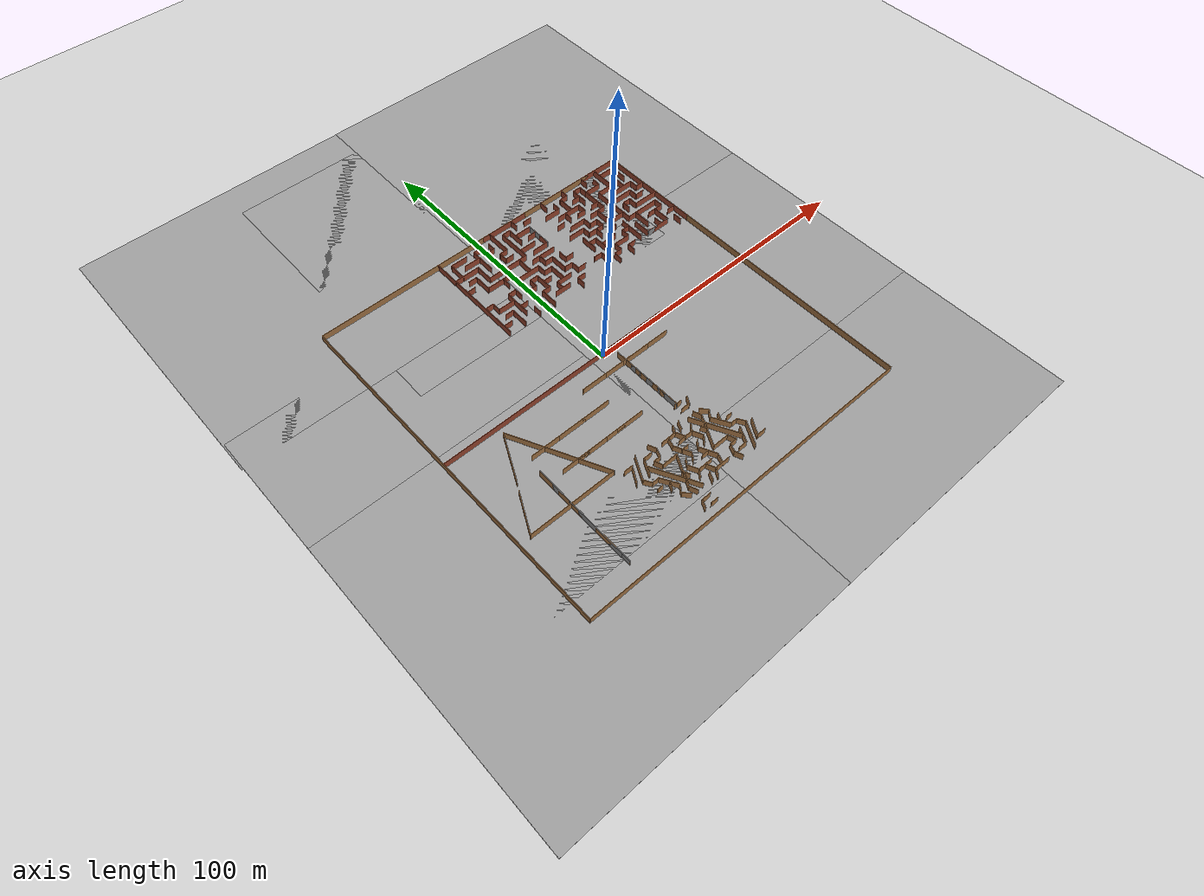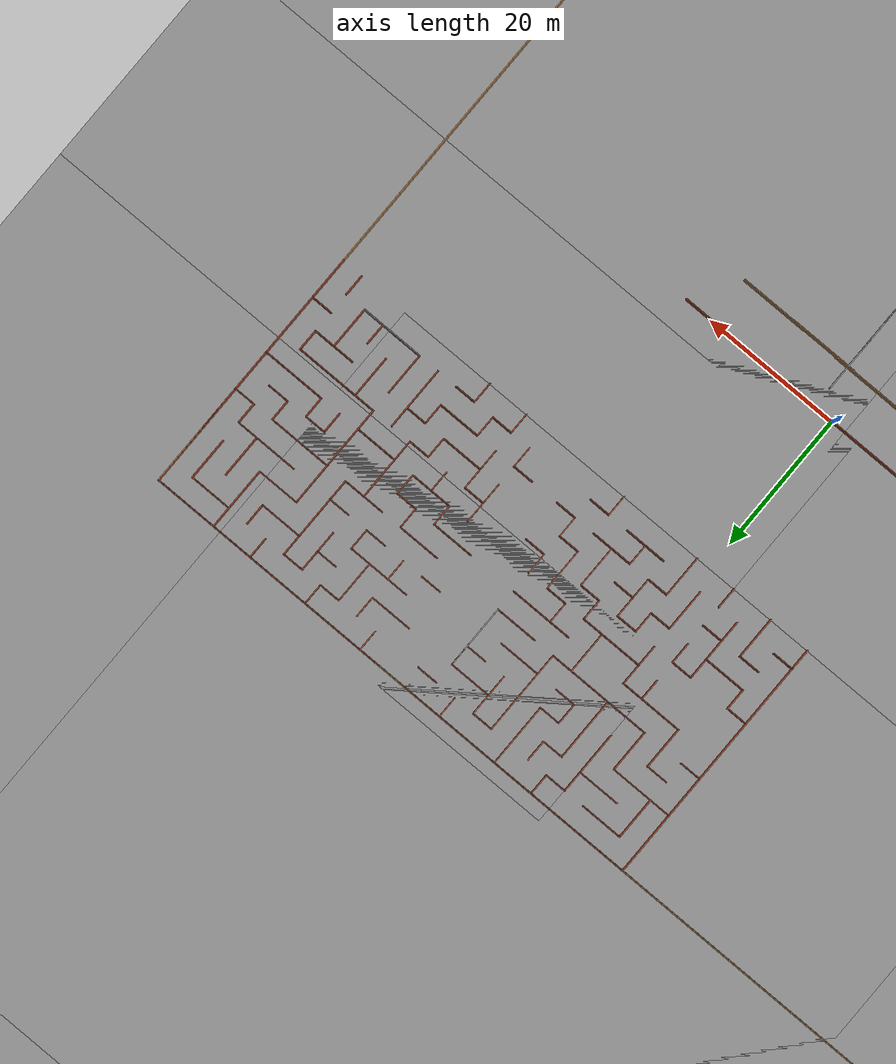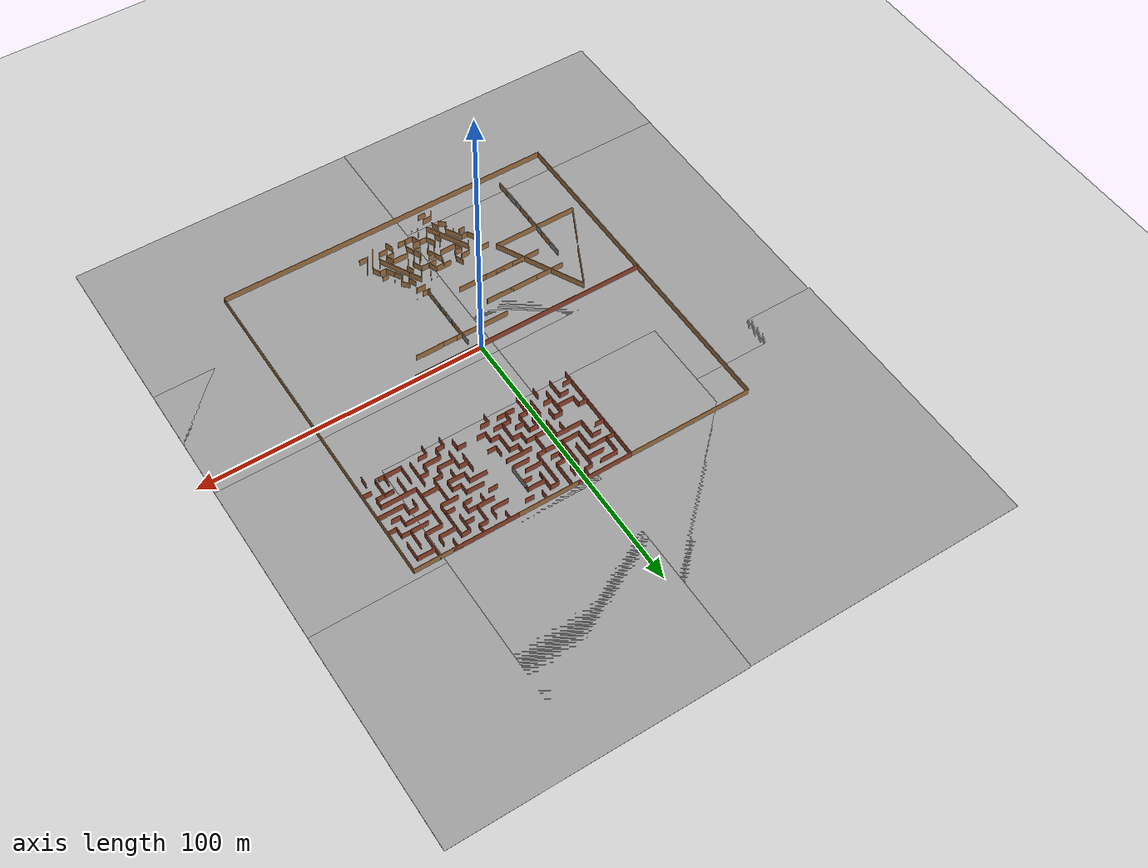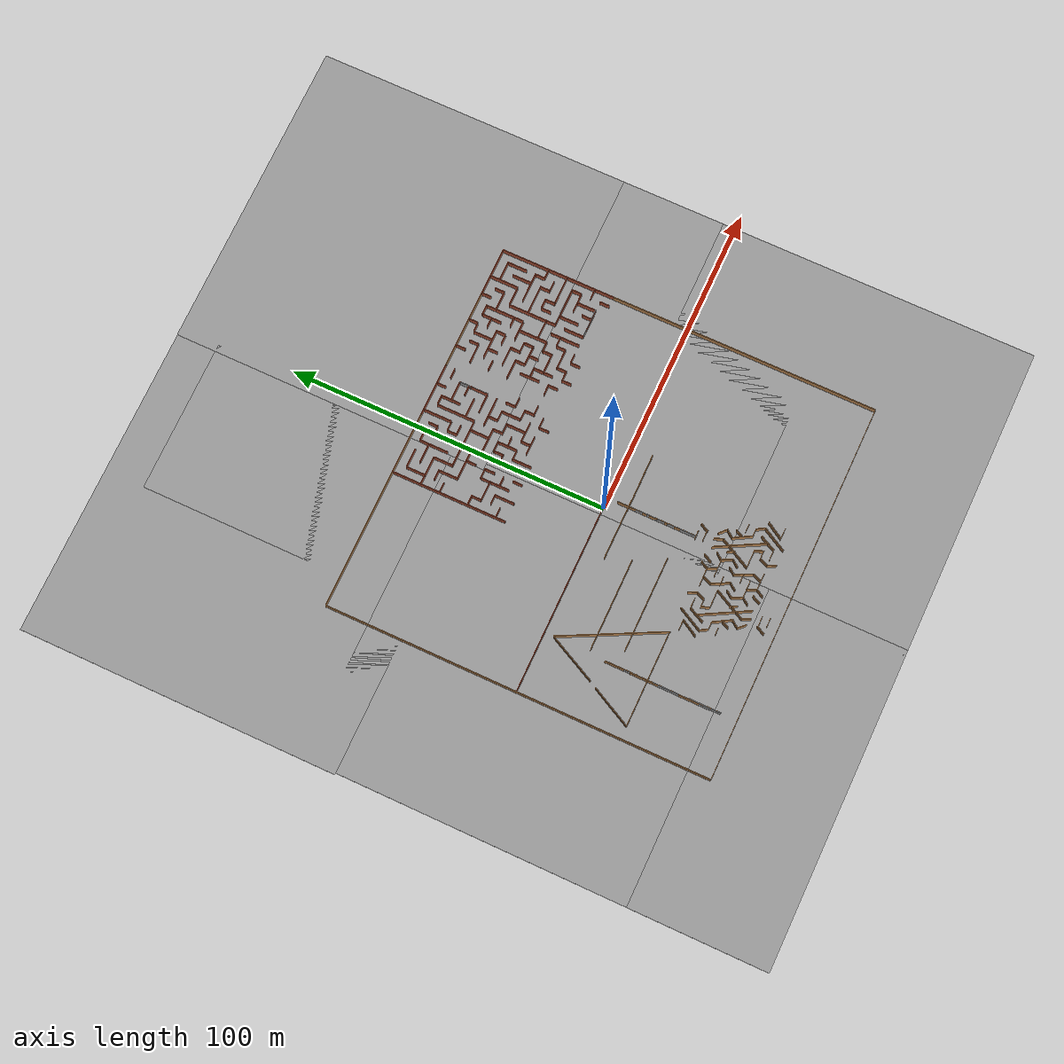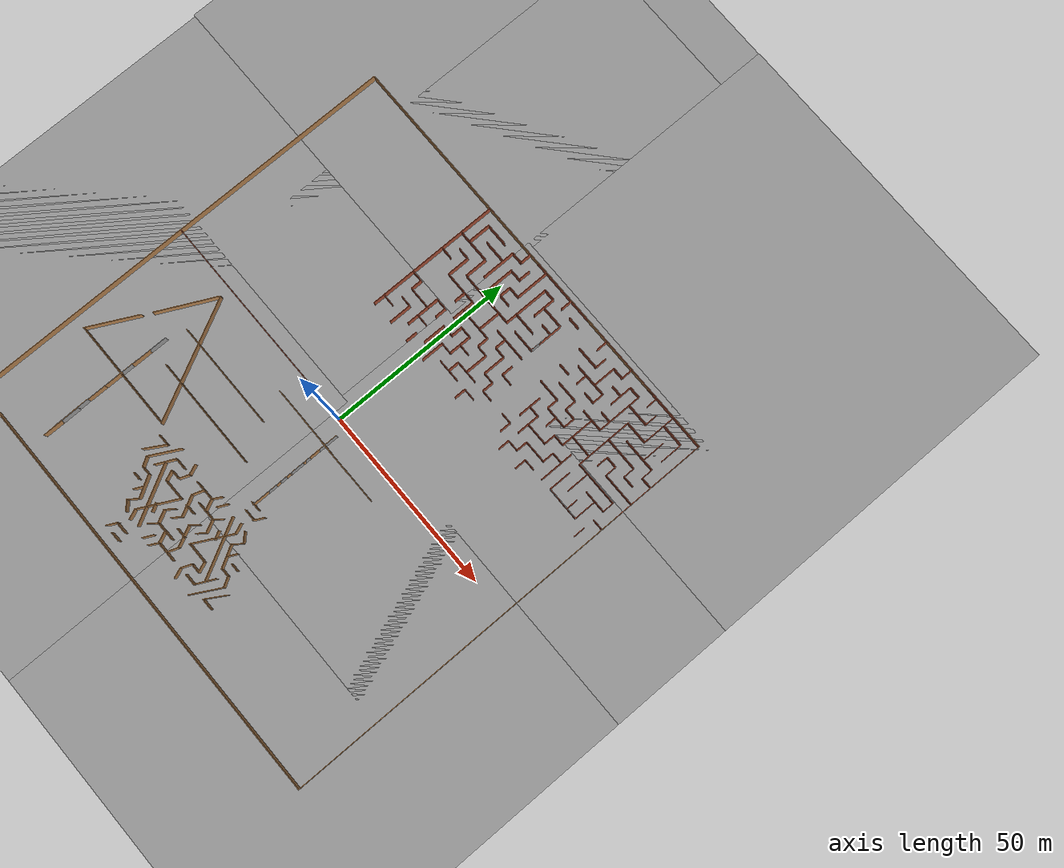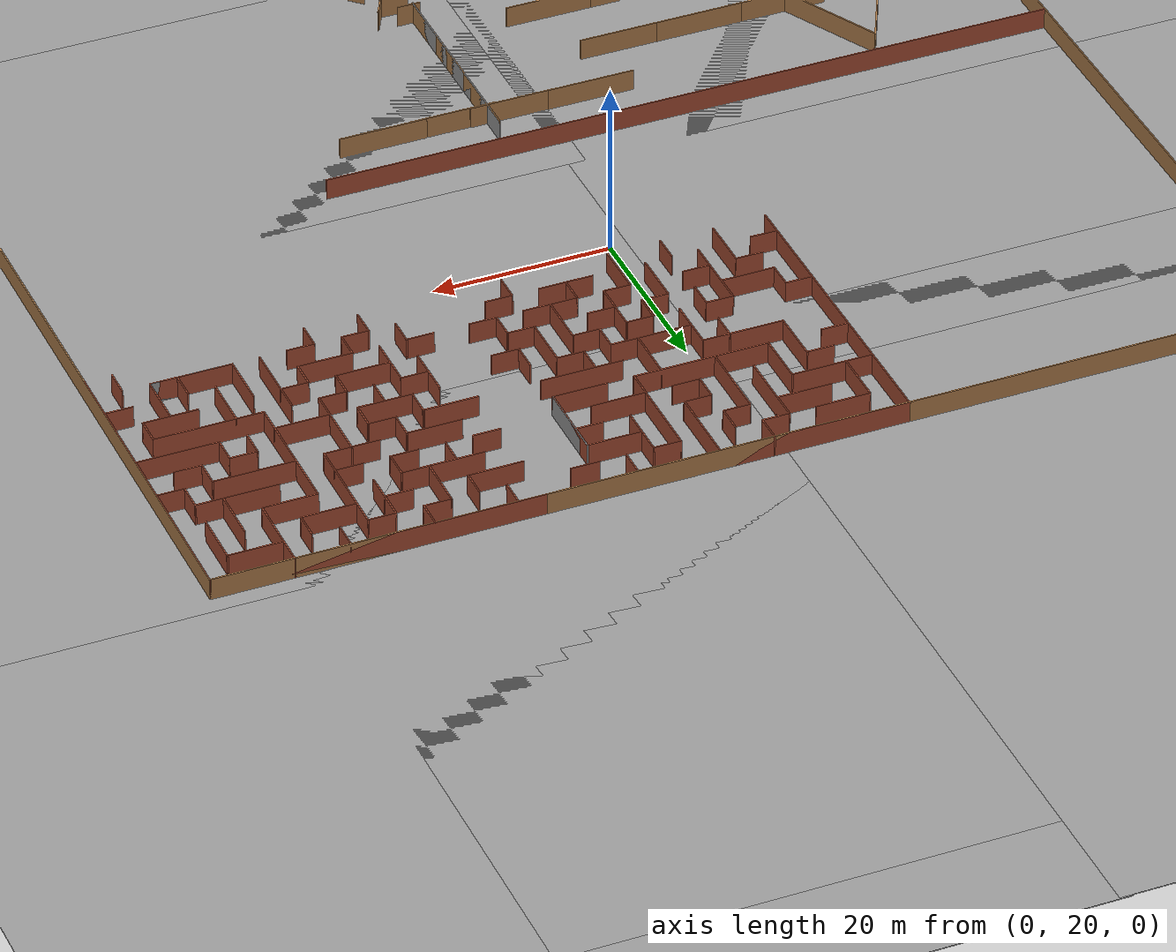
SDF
<sdf version="1.6">
 <world name="default">
  <light name="sun" type="directional">
   <pose>0 0 10 0 -0 0</pose>
   <diffuse>0.8 0.8 0.8 1</diffuse>
   <specular>0.2 0.2 0.2 1</specular>
   <attenuation>
    <range>1000</range>
    <constant>0.9</constant>
    <linear>0.01</linear>
    <quadratic>0.001</quadratic>
   </attenuation>
   <direction>-0.5 0.1 -0.9</direction>
  </light>
  <model name="ground_plane">
   <static>1</static>
   <link name="link">
    <collision name="collision">
     <geometry><plane><normal>0 0 1</normal><size>100 100</size></plane></geometry>
     <surface><friction><ode><mu>100</mu><mu2>50</mu2></ode></friction></surface>
    </collision>
    <visual name="visual">
     <cast_shadows>0</cast_shadows>
     <geometry><plane><normal>0 0 1</normal><size>100 100</size></plane></geometry>
     <material>
      <script><uri>file://media/materials/scripts/gazebo.material</uri><name>Gazebo/Grey</name></script>
     </material>
    </visual>
   </link>
  </model>
  <physics name="default_physics" default="0" type="ode">
   <max_step_size>0.001</max_step_size>
   <real_time_factor>1</real_time_factor>
   <real_time_update_rate>1000</real_time_update_rate>
  </physics>
  <scene><ambient>0.4 0.4 0.4 1</ambient><background>0.7 0.7 0.7 1</background><shadows>1</shadows></scene>
  <spherical_coordinates>
   <surface_model>EARTH_WGS84</surface_model>
   <latitude_deg>0</latitude_deg>
   <longitude_deg>0</longitude_deg>
   <elevation>0</elevation>
   <heading_deg>0</heading_deg>
  </spherical_coordinates>
  <model name="maze_final_2_0">
   <pose>42 42 0 0 -0 0</pose>
   <link name="Wall_10">
    <collision name="Wall_10_Collision">
     <geometry><box><size>3.15 0.15 2.5</size></box></geometry>
     <pose>0 0 1.25 0 -0 0</pose>
    </collision>
    <visual name="Wall_10_Visual">
     <pose>0 0 1.25 0 -0 0</pose>
     <geometry><box><size>3.15 0.15 2.5</size></box></geometry>
     <material>
      <script><uri>file://media/materials/scripts/gazebo.material</uri><name>Gazebo/Bricks</name></script>
      <ambient>1 1 1 1</ambient>
     </material>
    </visual>
    <pose>-16.5 -12 0 0 -0 0</pose>
   </link>
   <link name="Wall_100">
    <collision name="Wall_100_Collision">
     <geometry><box><size>3.15 0.15 2.5</size></box></geometry>
     <pose>0 0 1.25 0 -0 0</pose>
    </collision>
    <visual name="Wall_100_Visual">
     <pose>0 0 1.25 0 -0 0</pose>
     <geometry><box><size>3.15 0.15 2.5</size></box></geometry>
     <material>
      <script><uri>file://media/materials/scripts/gazebo.material</uri><name>Gazebo/Bricks</name></script>
      <ambient>1 1 1 1</ambient>
     </material>
    </visual>
    <pose>-4.5 12 0 0 -0 3.14159</pose>
   </link>
   <link name="Wall_102">
    <collision name="Wall_102_Collision">
     <geometry><box><size>9.15 0.15 2.5</size></box></geometry>
     <pose>0 0 1.25 0 -0 0</pose>
    </collision>
    <visual name="Wall_102_Visual">
     <pose>0 0 1.25 0 -0 0</pose>
     <geometry><box><size>9.15 0.15 2.5</size></box></geometry>
     <material>
      <script><uri>file://media/materials/scripts/gazebo.material</uri><name>Gazebo/Bricks</name></script>
      <ambient>1 1 1 1</ambient>
     </material>
    </visual>
    <pose>-0.0065 7.5 0 0 0 -1.57224</pose>
   </link>
   <link name="Wall_103">
    <collision name="Wall_103_Collision">
     <geometry><box><size>6.137 0.15 2.5</size></box></geometry>
     <pose>0 0 1.25 0 -0 0</pose>
    </collision>
    <visual name="Wall_103_Visual">
     <pose>0 0 1.25 0 -0 0</pose>
     <geometry><box><size>6.137 0.15 2.5</size></box></geometry>
     <material>
      <script><uri>file://media/materials/scripts/gazebo.material</uri><name>Gazebo/Bricks</name></script>
      <ambient>1 1 1 1</ambient>
     </material>
    </visual>
    <pose>-3.0065 3 0 0 -0 3.14159</pose>
   </link>
   <link name="Wall_105">
    <collision name="Wall_105_Collision">
     <geometry><box><size>3.15 0.15 2.5</size></box></geometry>
     <pose>0 0 1.25 0 -0 0</pose>
    </collision>
    <visual name="Wall_105_Visual">
     <pose>0 0 1.25 0 -0 0</pose>
     <geometry><box><size>3.15 0.15 2.5</size></box></geometry>
     <material>
      <script><uri>file://media/materials/scripts/gazebo.material</uri><name>Gazebo/Bricks</name></script>
      <ambient>1 1 1 1</ambient>
     </material>
    </visual>
    <pose>-1.5 6 0 0 -0 3.14159</pose>
   </link>
   <link name="Wall_108">
    <collision name="Wall_108_Collision">
     <geometry><box><size>6.15 0.15 2.5</size></box></geometry>
     <pose>0 0 1.25 0 -0 0</pose>
    </collision>
    <visual name="Wall_108_Visual">
     <pose>0 0 1.25 0 -0 0</pose>
     <geometry><box><size>6.15 0.15 2.5</size></box></geometry>
     <material>
      <script><uri>file://media/materials/scripts/gazebo.material</uri><name>Gazebo/Bricks</name></script>
      <ambient>1 1 1 1</ambient>
     </material>
    </visual>
    <pose>1e-06 -3 0 0 -0 3.14159</pose>
   </link>
   <link name="Wall_110">
    <collision name="Wall_110_Collision">
     <geometry><box><size>9.15 0.15 2.5</size></box></geometry>
     <pose>0 0 1.25 0 -0 0</pose>
    </collision>
    <visual name="Wall_110_Visual">
     <pose>0 0 1.25 0 -0 0</pose>
     <geometry><box><size>9.15 0.15 2.5</size></box></geometry>
     <material>
      <script><uri>file://media/materials/scripts/gazebo.material</uri><name>Gazebo/Bricks</name></script>
      <ambient>1 1 1 1</ambient>
     </material>
    </visual>
    <pose>-3 -1.5 0 0 -0 1.5708</pose>
   </link>
   <link name="Wall_112">
    <collision name="Wall_112_Collision">
     <geometry><box><size>3.15 0.15 2.5</size></box></geometry>
     <pose>0 0 1.25 0 -0 0</pose>
    </collision>
    <visual name="Wall_112_Visual">
     <pose>0 0 1.25 0 -0 0</pose>
     <geometry><box><size>3.15 0.15 2.5</size></box></geometry>
     <material>
      <script><uri>file://media/materials/scripts/gazebo.material</uri><name>Gazebo/Bricks</name></script>
      <ambient>1 1 1 1</ambient>
     </material>
    </visual>
    <pose>-4.5 -6 0 0 -0 3.14159</pose>
   </link>
   <link name="Wall_113">
    <collision name="Wall_113_Collision">
     <geometry><box><size>3.15 0.15 2.5</size></box></geometry>
     <pose>0 0 1.25 0 -0 0</pose>
    </collision>
    <visual name="Wall_113_Visual">
     <pose>0 0 1.25 0 -0 0</pose>
     <geometry><box><size>3.15 0.15 2.5</size></box></geometry>
     <material>
      <script><uri>file://media/materials/scripts/gazebo.material</uri><name>Gazebo/Bricks</name></script>
      <ambient>1 1 1 1</ambient>
     </material>
    </visual>
    <pose>-6 -7.5 0 0 0 -1.5708</pose>
   </link>
   <link name="Wall_114">
    <collision name="Wall_114_Collision">
     <geometry><box><size>6.15 0.15 2.5</size></box></geometry>
     <pose>0 0 1.25 0 -0 0</pose>
    </collision>
    <visual name="Wall_114_Visual">
     <pose>0 0 1.25 0 -0 0</pose>
     <geometry><box><size>6.15 0.15 2.5</size></box></geometry>
     <material>
      <script><uri>file://media/materials/scripts/gazebo.material</uri><name>Gazebo/Bricks</name></script>
      <ambient>1 1 1 1</ambient>
     </material>
    </visual>
    <pose>-9 -9 0 0 -0 3.14159</pose>
   </link>
   <link name="Wall_116">
    <collision name="Wall_116_Collision">
     <geometry><box><size>6.15 0.15 2.5</size></box></geometry>
     <pose>0 0 1.25 0 -0 0</pose>
    </collision>
    <visual name="Wall_116_Visual">
     <pose>0 0 1.25 0 -0 0</pose>
     <geometry><box><size>6.15 0.15 2.5</size></box></geometry>
     <material>
      <script><uri>file://media/materials/scripts/gazebo.material</uri><name>Gazebo/Bricks</name></script>
      <ambient>1 1 1 1</ambient>
     </material>
    </visual>
    <pose>-12 -9 0 0 -0 1.5708</pose>
   </link>
   <link name="Wall_117">
    <collision name="Wall_117_Collision">
     <geometry><box><size>3.15 0.15 2.5</size></box></geometry>
     <pose>0 0 1.25 0 -0 0</pose>
    </collision>
    <visual name="Wall_117_Visual">
     <pose>0 0 1.25 0 -0 0</pose>
     <geometry><box><size>3.15 0.15 2.5</size></box></geometry>
     <material>
      <script><uri>file://media/materials/scripts/gazebo.material</uri><name>Gazebo/Bricks</name></script>
      <ambient>1 1 1 1</ambient>
     </material>
    </visual>
    <pose>-13.5 -6 0 0 -0 3.14159</pose>
   </link>
   <link name="Wall_119">
    <collision name="Wall_119_Collision">
     <geometry><box><size>6.15 0.15 2.5</size></box></geometry>
     <pose>0 0 1.25 0 -0 0</pose>
    </collision>
    <visual name="Wall_119_Visual">
     <pose>0 0 1.25 0 -0 0</pose>
     <geometry><box><size>6.15 0.15 2.5</size></box></geometry>
     <material>
      <script><uri>file://media/materials/scripts/gazebo.material</uri><name>Gazebo/Bricks</name></script>
      <ambient>1 1 1 1</ambient>
     </material>
    </visual>
    <pose>-15 -6 0 0 0 -1.5708</pose>
   </link>
   <link name="Wall_12">
    <collision name="Wall_12_Collision">
     <geometry><box><size>6.15 0.15 2.5</size></box></geometry>
     <pose>0 0 1.25 0 -0 0</pose>
    </collision>
    <visual name="Wall_12_Visual">
     <pose>0 0 1.25 0 -0 0</pose>
     <geometry><box><size>6.15 0.15 2.5</size></box></geometry>
     <material>
      <script><uri>file://media/materials/scripts/gazebo.material</uri><name>Gazebo/Bricks</name></script>
      <ambient>1 1 1 1</ambient>
     </material>
    </visual>
    <pose>-15 -1e-06 0 0 -0 0</pose>
   </link>
   <link name="Wall_121">
    <collision name="Wall_121_Collision">
     <geometry><box><size>3.13703 0.15 2.5</size></box></geometry>
     <pose>0 0 1.25 0 -0 0</pose>
    </collision>
    <visual name="Wall_121_Visual">
     <pose>0 0 1.25 0 -0 0</pose>
     <geometry><box><size>3.13703 0.15 2.5</size></box></geometry>
     <material>
      <script><uri>file://media/materials/scripts/gazebo.material</uri><name>Gazebo/Bricks</name></script>
      <ambient>1 1 1 1</ambient>
     </material>
    </visual>
    <pose>-12.0065 -1.4935 0 0 0 -1.57515</pose>
   </link>
   <link name="Wall_122">
    <collision name="Wall_122_Collision">
     <geometry><box><size>6.16301 0.15 2.5</size></box></geometry>
     <pose>0 0 1.25 0 -0 0</pose>
    </collision>
    <visual name="Wall_122_Visual">
     <pose>0 0 1.25 0 -0 0</pose>
     <geometry><box><size>6.16301 0.15 2.5</size></box></geometry>
     <material>
      <script><uri>file://media/materials/scripts/gazebo.material</uri><name>Gazebo/Bricks</name></script>
      <ambient>1 1 1 1</ambient>
     </material>
    </visual>
    <pose>-9.0065 -2.9935 0 0 0 -0.002162</pose>
   </link>
   <link name="Wall_123">
    <collision name="Wall_123_Collision">
     <geometry><box><size>3.15 0.15 2.5</size></box></geometry>
     <pose>0 0 1.25 0 -0 0</pose>
    </collision>
    <visual name="Wall_123_Visual">
     <pose>0 0 1.25 0 -0 0</pose>
     <geometry><box><size>3.15 0.15 2.5</size></box></geometry>
     <material>
      <script><uri>file://media/materials/scripts/gazebo.material</uri><name>Gazebo/Bricks</name></script>
      <ambient>1 1 1 1</ambient>
     </material>
    </visual>
    <pose>-6 -1.5 0 0 -0 1.5708</pose>
   </link>
   <link name="Wall_124">
    <collision name="Wall_124_Collision">
     <geometry><box><size>3.15 0.15 2.5</size></box></geometry>
     <pose>0 0 1.25 0 -0 0</pose>
    </collision>
    <visual name="Wall_124_Visual">
     <pose>0 0 1.25 0 -0 0</pose>
     <geometry><box><size>3.15 0.15 2.5</size></box></geometry>
     <material>
      <script><uri>file://media/materials/scripts/gazebo.material</uri><name>Gazebo/Bricks</name></script>
      <ambient>1 1 1 1</ambient>
     </material>
    </visual>
    <pose>-7.5 -1e-06 0 0 -0 3.14159</pose>
   </link>
   <link name="Wall_125">
    <collision name="Wall_125_Collision">
     <geometry><box><size>3.15 0.15 2.5</size></box></geometry>
     <pose>0 0 1.25 0 -0 0</pose>
    </collision>
    <visual name="Wall_125_Visual">
     <pose>0 0 1.25 0 -0 0</pose>
     <geometry><box><size>3.15 0.15 2.5</size></box></geometry>
     <material>
      <script><uri>file://media/materials/scripts/gazebo.material</uri><name>Gazebo/Bricks</name></script>
      <ambient>1 1 1 1</ambient>
     </material>
    </visual>
    <pose>-9 1.5 0 0 -0 1.5708</pose>
   </link>
   <link name="Wall_127">
    <collision name="Wall_127_Collision">
     <geometry><box><size>6.15 0.15 2.5</size></box></geometry>
     <pose>0 0 1.25 0 -0 0</pose>
    </collision>
    <visual name="Wall_127_Visual">
     <pose>0 0 1.25 0 -0 0</pose>
     <geometry><box><size>6.15 0.15 2.5</size></box></geometry>
     <material>
      <script><uri>file://media/materials/scripts/gazebo.material</uri><name>Gazebo/Bricks</name></script>
      <ambient>1 1 1 1</ambient>
     </material>
    </visual>
    <pose>-12 3 0 0 -0 3.14159</pose>
   </link>
   <link name="Wall_129">
    <collision name="Wall_129_Collision">
     <geometry><box><size>3.15 0.15 2.5</size></box></geometry>
     <pose>0 0 1.25 0 -0 0</pose>
    </collision>
    <visual name="Wall_129_Visual">
     <pose>0 0 1.25 0 -0 0</pose>
     <geometry><box><size>3.15 0.15 2.5</size></box></geometry>
     <material>
      <script><uri>file://media/materials/scripts/gazebo.material</uri><name>Gazebo/Bricks</name></script>
      <ambient>1 1 1 1</ambient>
     </material>
    </visual>
    <pose>-9 -4.5 0 0 0 -1.5708</pose>
   </link>
   <link name="Wall_131">
    <collision name="Wall_131_Collision">
     <geometry><box><size>3.15 0.15 2.5</size></box></geometry>
     <pose>0 0 1.25 0 -0 0</pose>
    </collision>
    <visual name="Wall_131_Visual">
     <pose>0 0 1.25 0 -0 0</pose>
     <geometry><box><size>3.15 0.15 2.5</size></box></geometry>
     <material>
      <script><uri>file://media/materials/scripts/gazebo.material</uri><name>Gazebo/Bricks</name></script>
      <ambient>1 1 1 1</ambient>
     </material>
    </visual>
    <pose>-6 16.5 0 0 0 -1.5708</pose>
   </link>
   <link name="Wall_132">
    <collision name="Wall_132_Collision">
     <geometry><box><size>3.15 0.15 2.5</size></box></geometry>
     <pose>0 0 1.25 0 -0 0</pose>
    </collision>
    <visual name="Wall_132_Visual">
     <pose>0 0 1.25 0 -0 0</pose>
     <geometry><box><size>3.15 0.15 2.5</size></box></geometry>
     <material>
      <script><uri>file://media/materials/scripts/gazebo.material</uri><name>Gazebo/Bricks</name></script>
      <ambient>1 1 1 1</ambient>
     </material>
    </visual>
    <pose>-7.5 15 0 0 -0 3.14159</pose>
   </link>
   <link name="Wall_133">
    <collision name="Wall_133_Collision">
     <geometry><box><size>6.15 0.15 2.5</size></box></geometry>
     <pose>0 0 1.25 0 -0 0</pose>
    </collision>
    <visual name="Wall_133_Visual">
     <pose>0 0 1.25 0 -0 0</pose>
     <geometry><box><size>6.15 0.15 2.5</size></box></geometry>
     <material>
      <script><uri>file://media/materials/scripts/gazebo.material</uri><name>Gazebo/Bricks</name></script>
      <ambient>1 1 1 1</ambient>
     </material>
    </visual>
    <pose>-9 12 0 0 0 -1.5708</pose>
   </link>
   <link name="Wall_135">
    <collision name="Wall_135_Collision">
     <geometry><box><size>3.15 0.15 2.5</size></box></geometry>
     <pose>0 0 1.25 0 -0 0</pose>
    </collision>
    <visual name="Wall_135_Visual">
     <pose>0 0 1.25 0 -0 0</pose>
     <geometry><box><size>3.15 0.15 2.5</size></box></geometry>
     <material>
      <script><uri>file://media/materials/scripts/gazebo.material</uri><name>Gazebo/Bricks</name></script>
      <ambient>1 1 1 1</ambient>
     </material>
    </visual>
    <pose>-7.5 6 0 0 -0 0</pose>
   </link>
   <link name="Wall_136">
    <collision name="Wall_136_Collision">
     <geometry><box><size>3.15 0.15 2.5</size></box></geometry>
     <pose>0 0 1.25 0 -0 0</pose>
    </collision>
    <visual name="Wall_136_Visual">
     <pose>0 0 1.25 0 -0 0</pose>
     <geometry><box><size>3.15 0.15 2.5</size></box></geometry>
     <material>
      <script><uri>file://media/materials/scripts/gazebo.material</uri><name>Gazebo/Bricks</name></script>
      <ambient>1 1 1 1</ambient>
     </material>
    </visual>
    <pose>-6 7.5 0 0 -0 1.5708</pose>
   </link>
   <link name="Wall_137">
    <collision name="Wall_137_Collision">
     <geometry><box><size>9.15 0.15 2.5</size></box></geometry>
     <pose>0 0 1.25 0 -0 0</pose>
    </collision>
    <visual name="Wall_137_Visual">
     <pose>0 0 1.25 0 -0 0</pose>
     <geometry><box><size>9.15 0.15 2.5</size></box></geometry>
     <material>
      <script><uri>file://media/materials/scripts/gazebo.material</uri><name>Gazebo/Bricks</name></script>
      <ambient>1 1 1 1</ambient>
     </material>
    </visual>
    <pose>-10.5 9 0 0 -0 3.14159</pose>
   </link>
   <link name="Wall_139">
    <collision name="Wall_139_Collision">
     <geometry><box><size>3.15 0.15 2.5</size></box></geometry>
     <pose>0 0 1.25 0 -0 0</pose>
    </collision>
    <visual name="Wall_139_Visual">
     <pose>0 0 1.25 0 -0 0</pose>
     <geometry><box><size>3.15 0.15 2.5</size></box></geometry>
     <material>
      <script><uri>file://media/materials/scripts/gazebo.material</uri><name>Gazebo/Bricks</name></script>
      <ambient>1 1 1 1</ambient>
     </material>
    </visual>
    <pose>-12 7.5 0 0 0 -1.5708</pose>
   </link>
   <link name="Wall_14">
    <collision name="Wall_14_Collision">
     <geometry><box><size>3.15 0.15 2.5</size></box></geometry>
     <pose>0 0 1.25 0 -0 0</pose>
    </collision>
    <visual name="Wall_14_Visual">
     <pose>0 0 1.25 0 -0 0</pose>
     <geometry><box><size>3.15 0.15 2.5</size></box></geometry>
     <material>
      <script><uri>file://media/materials/scripts/gazebo.material</uri><name>Gazebo/Bricks</name></script>
      <ambient>1 1 1 1</ambient>
     </material>
    </visual>
    <pose>-16.5 6 0 0 -0 0</pose>
   </link>
   <link name="Wall_141">
    <collision name="Wall_141_Collision">
     <geometry><box><size>3.15 0.15 2.5</size></box></geometry>
     <pose>0 0 1.25 0 -0 0</pose>
    </collision>
    <visual name="Wall_141_Visual">
     <pose>0 0 1.25 0 -0 0</pose>
     <geometry><box><size>3.15 0.15 2.5</size></box></geometry>
     <material>
      <script><uri>file://media/materials/scripts/gazebo.material</uri><name>Gazebo/Bricks</name></script>
      <ambient>1 1 1 1</ambient>
     </material>
    </visual>
    <pose>-15 16.5 0 0 -0 1.5708</pose>
   </link>
   <link name="Wall_143">
    <collision name="Wall_143_Collision">
     <geometry><box><size>3.15 0.15 2.5</size></box></geometry>
     <pose>0 0 1.25 0 -0 0</pose>
    </collision>
    <visual name="Wall_143_Visual">
     <pose>0 0 1.25 0 -0 0</pose>
     <geometry><box><size>3.15 0.15 2.5</size></box></geometry>
     <material>
      <script><uri>file://media/materials/scripts/gazebo.material</uri><name>Gazebo/Bricks</name></script>
      <ambient>1 1 1 1</ambient>
     </material>
    </visual>
    <pose>-12 13.5 0 0 -0 1.5708</pose>
   </link>
   <link name="Wall_16">
    <collision name="Wall_16_Collision">
     <geometry><box><size>6.15 0.15 2.5</size></box></geometry>
     <pose>0 0 1.25 0 -0 0</pose>
    </collision>
    <visual name="Wall_16_Visual">
     <pose>0 0 1.25 0 -0 0</pose>
     <geometry><box><size>6.15 0.15 2.5</size></box></geometry>
     <material>
      <script><uri>file://media/materials/scripts/gazebo.material</uri><name>Gazebo/Bricks</name></script>
      <ambient>1 1 1 1</ambient>
     </material>
    </visual>
    <pose>-15 12 0 0 -0 0</pose>
   </link>
   <link name="Wall_18">
    <collision name="Wall_18_Collision">
     <geometry><box><size>3.15 0.15 2.5</size></box></geometry>
     <pose>0 0 1.25 0 -0 0</pose>
    </collision>
    <visual name="Wall_18_Visual">
     <pose>0 0 1.25 0 -0 0</pose>
     <geometry><box><size>3.15 0.15 2.5</size></box></geometry>
     <material>
      <script><uri>file://media/materials/scripts/gazebo.material</uri><name>Gazebo/Bricks</name></script>
      <ambient>1 1 1 1</ambient>
     </material>
    </visual>
    <pose>-12 -16.5 0 0 -0 1.5708</pose>
   </link>
   <link name="Wall_20">
    <collision name="Wall_20_Collision">
     <geometry><box><size>3.15 0.15 2.5</size></box></geometry>
     <pose>0 0 1.25 0 -0 0</pose>
    </collision>
    <visual name="Wall_20_Visual">
     <pose>0 0 1.25 0 -0 0</pose>
     <geometry><box><size>3.15 0.15 2.5</size></box></geometry>
     <material>
      <script><uri>file://media/materials/scripts/gazebo.material</uri><name>Gazebo/Bricks</name></script>
      <ambient>1 1 1 1</ambient>
     </material>
    </visual>
    <pose>-10.5 -15 0 0 -0 0</pose>
   </link>
   <link name="Wall_22">
    <collision name="Wall_22_Collision">
     <geometry><box><size>6.15 0.15 2.5</size></box></geometry>
     <pose>0 0 1.25 0 -0 0</pose>
    </collision>
    <visual name="Wall_22_Visual">
     <pose>0 0 1.25 0 -0 0</pose>
     <geometry><box><size>6.15 0.15 2.5</size></box></geometry>
     <material>
      <script><uri>file://media/materials/scripts/gazebo.material</uri><name>Gazebo/Bricks</name></script>
      <ambient>1 1 1 1</ambient>
     </material>
    </visual>
    <pose>-6 -12 0 0 -0 0</pose>
   </link>
   <link name="Wall_24">
    <collision name="Wall_24_Collision">
     <geometry><box><size>3.15 0.15 2.5</size></box></geometry>
     <pose>0 0 1.25 0 -0 0</pose>
    </collision>
    <visual name="Wall_24_Visual">
     <pose>0 0 1.25 0 -0 0</pose>
     <geometry><box><size>3.15 0.15 2.5</size></box></geometry>
     <material>
      <script><uri>file://media/materials/scripts/gazebo.material</uri><name>Gazebo/Bricks</name></script>
      <ambient>1 1 1 1</ambient>
     </material>
    </visual>
    <pose>-9 -13.5 0 0 0 -1.5708</pose>
   </link>
   <link name="Wall_26">
    <collision name="Wall_26_Collision">
     <geometry><box><size>3.15 0.15 2.5</size></box></geometry>
     <pose>0 0 1.25 0 -0 0</pose>
    </collision>
    <visual name="Wall_26_Visual">
     <pose>0 0 1.25 0 -0 0</pose>
     <geometry><box><size>3.15 0.15 2.5</size></box></geometry>
     <material>
      <script><uri>file://media/materials/scripts/gazebo.material</uri><name>Gazebo/Bricks</name></script>
      <ambient>1 1 1 1</ambient>
     </material>
    </visual>
    <pose>-6 -16.5 0 0 -0 1.5708</pose>
   </link>
   <link name="Wall_28">
    <collision name="Wall_28_Collision">
     <geometry><box><size>3.15 0.15 2.5</size></box></geometry>
     <pose>0 0 1.25 0 -0 0</pose>
    </collision>
    <visual name="Wall_28_Visual">
     <pose>0 0 1.25 0 -0 0</pose>
     <geometry><box><size>3.15 0.15 2.5</size></box></geometry>
     <material>
      <script><uri>file://media/materials/scripts/gazebo.material</uri><name>Gazebo/Bricks</name></script>
      <ambient>1 1 1 1</ambient>
     </material>
    </visual>
    <pose>-4.5 -15 0 0 -0 0</pose>
   </link>
   <link name="Wall_32">
    <collision name="Wall_32_Collision">
     <geometry><box><size>9.15 0.15 2.5</size></box></geometry>
     <pose>0 0 1.25 0 -0 0</pose>
    </collision>
    <visual name="Wall_32_Visual">
     <pose>0 0 1.25 0 -0 0</pose>
     <geometry><box><size>9.15 0.15 2.5</size></box></geometry>
     <material>
      <script><uri>file://media/materials/scripts/gazebo.material</uri><name>Gazebo/Bricks</name></script>
      <ambient>1 1 1 1</ambient>
     </material>
    </visual>
    <pose>1e-06 -10.5 0 0 -0 1.5708</pose>
   </link>
   <link name="Wall_34">
    <collision name="Wall_34_Collision">
     <geometry><box><size>3.15 0.15 2.5</size></box></geometry>
     <pose>0 0 1.25 0 -0 0</pose>
    </collision>
    <visual name="Wall_34_Visual">
     <pose>0 0 1.25 0 -0 0</pose>
     <geometry><box><size>3.15 0.15 2.5</size></box></geometry>
     <material>
      <script><uri>file://media/materials/scripts/gazebo.material</uri><name>Gazebo/Bricks</name></script>
      <ambient>1 1 1 1</ambient>
     </material>
    </visual>
    <pose>-1.5 -9 0 0 -0 3.14159</pose>
   </link>
   <link name="Wall_36">
    <collision name="Wall_36_Collision">
     <geometry><box><size>3.15 0.15 2.5</size></box></geometry>
     <pose>0 0 1.25 0 -0 0</pose>
    </collision>
    <visual name="Wall_36_Visual">
     <pose>0 0 1.25 0 -0 0</pose>
     <geometry><box><size>3.15 0.15 2.5</size></box></geometry>
     <material>
      <script><uri>file://media/materials/scripts/gazebo.material</uri><name>Gazebo/Bricks</name></script>
      <ambient>1 1 1 1</ambient>
     </material>
    </visual>
    <pose>-3 -10.5 0 0 -0 1.5708</pose>
   </link>
   <link name="Wall_4">
    <collision name="Wall_4_Collision">
     <geometry><box><size>36.15 0.15 2.5</size></box></geometry>
     <pose>0 0 1.25 0 -0 0</pose>
    </collision>
    <visual name="Wall_4_Visual">
     <pose>0 0 1.25 0 -0 0</pose>
     <geometry><box><size>36.15 0.15 2.5</size></box></geometry>
     <material>
      <script><uri>file://media/materials/scripts/gazebo.material</uri><name>Gazebo/Bricks</name></script>
      <ambient>1 1 1 1</ambient>
     </material>
    </visual>
    <pose>18 -1e-06 0 0 0 -1.5708</pose>
   </link>
   <link name="Wall_40">
    <collision name="Wall_40_Collision">
     <geometry><box><size>9.15 0.15 2.5</size></box></geometry>
     <pose>0 0 1.25 0 -0 0</pose>
    </collision>
    <visual name="Wall_40_Visual">
     <pose>0 0 1.25 0 -0 0</pose>
     <geometry><box><size>9.15 0.15 2.5</size></box></geometry>
     <material>
      <script><uri>file://media/materials/scripts/gazebo.material</uri><name>Gazebo/Grey</name></script>
      <ambient>1 1 1 1</ambient>
     </material>
    </visual>
    <pose>7.5 -15 0 0 -0 0</pose>
   </link>
   <link name="Wall_43">
    <collision name="Wall_43_Collision">
     <geometry><box><size>9.15 0.15 2.5</size></box></geometry>
     <pose>0 0 1.25 0 -0 0</pose>
    </collision>
    <visual name="Wall_43_Visual">
     <pose>0 0 1.25 0 -0 0</pose>
     <geometry><box><size>9.15 0.15 2.5</size></box></geometry>
     <material>
      <script><uri>file://media/materials/scripts/gazebo.material</uri><name>Gazebo/Bricks</name></script>
      <ambient>1 1 1 1</ambient>
     </material>
    </visual>
    <pose>9 13.5 0 0 0 -1.5708</pose>
   </link>
   <link name="Wall_45">
    <collision name="Wall_45_Collision">
     <geometry><box><size>6.15 0.15 2.5</size></box></geometry>
     <pose>0 0 1.25 0 -0 0</pose>
    </collision>
    <visual name="Wall_45_Visual">
     <pose>0 0 1.25 0 -0 0</pose>
     <geometry><box><size>6.15 0.15 2.5</size></box></geometry>
     <material>
      <script><uri>file://media/materials/scripts/gazebo.material</uri><name>Gazebo/Bricks</name></script>
      <ambient>1 1 1 1</ambient>
     </material>
    </visual>
    <pose>6 9 0 0 -0 3.14159</pose>
   </link>
   <link name="Wall_47">
    <collision name="Wall_47_Collision">
     <geometry><box><size>15.15 0.15 2.5</size></box></geometry>
     <pose>0 0 1.25 0 -0 0</pose>
    </collision>
    <visual name="Wall_47_Visual">
     <pose>0 0 1.25 0 -0 0</pose>
     <geometry><box><size>15.15 0.15 2.5</size></box></geometry>
     <material>
      <script><uri>file://media/materials/scripts/gazebo.material</uri><name>Gazebo/Bricks</name></script>
      <ambient>1 1 1 1</ambient>
     </material>
    </visual>
    <pose>3 1.5 0 0 0 -1.5708</pose>
   </link>
   <link name="Wall_49">
    <collision name="Wall_49_Collision">
     <geometry><box><size>12.15 0.15 2.5</size></box></geometry>
     <pose>0 0 1.25 0 -0 0</pose>
    </collision>
    <visual name="Wall_49_Visual">
     <pose>0 0 1.25 0 -0 0</pose>
     <geometry><box><size>12.15 0.15 2.5</size></box></geometry>
     <material>
      <script><uri>file://media/materials/scripts/gazebo.material</uri><name>Gazebo/Bricks</name></script>
      <ambient>1 1 1 1</ambient>
     </material>
    </visual>
    <pose>9 -6 0 0 -0 0</pose>
   </link>
   <link name="Wall_51">
    <collision name="Wall_51_Collision">
     <geometry><box><size>3.15 0.15 2.5</size></box></geometry>
     <pose>0 0 1.25 0 -0 0</pose>
    </collision>
    <visual name="Wall_51_Visual">
     <pose>0 0 1.25 0 -0 0</pose>
     <geometry><box><size>3.15 0.15 2.5</size></box></geometry>
     <material>
      <script><uri>file://media/materials/scripts/gazebo.material</uri><name>Gazebo/Bricks</name></script>
      <ambient>1 1 1 1</ambient>
     </material>
    </visual>
    <pose>15 -7.5 0 0 0 -1.5708</pose>
   </link>
   <link name="Wall_53">
    <collision name="Wall_53_Collision">
     <geometry><box><size>6.15 0.15 2.5</size></box></geometry>
     <pose>0 0 1.25 0 -0 0</pose>
    </collision>
    <visual name="Wall_53_Visual">
     <pose>0 0 1.25 0 -0 0</pose>
     <geometry><box><size>6.15 0.15 2.5</size></box></geometry>
     <material>
      <script><uri>file://media/materials/scripts/gazebo.material</uri><name>Gazebo/Bricks</name></script>
      <ambient>1 1 1 1</ambient>
     </material>
    </visual>
    <pose>12 -9 0 0 -0 3.14159</pose>
   </link>
   <link name="Wall_55">
    <collision name="Wall_55_Collision">
     <geometry><box><size>6.15 0.15 2.5</size></box></geometry>
     <pose>0 0 1.25 0 -0 0</pose>
    </collision>
    <visual name="Wall_55_Visual">
     <pose>0 0 1.25 0 -0 0</pose>
     <geometry><box><size>6.15 0.15 2.5</size></box></geometry>
     <material>
      <script><uri>file://media/materials/scripts/gazebo.material</uri><name>Gazebo/Bricks</name></script>
      <ambient>1 1 1 1</ambient>
     </material>
    </visual>
    <pose>12 -12 0 0 0 -1.5708</pose>
   </link>
   <link name="Wall_57">
    <collision name="Wall_57_Collision">
     <geometry><box><size>9.15 0.15 2.5</size></box></geometry>
     <pose>0 0 1.25 0 -0 0</pose>
    </collision>
    <visual name="Wall_57_Visual">
     <pose>0 0 1.25 0 -0 0</pose>
     <geometry><box><size>9.15 0.15 2.5</size></box></geometry>
     <material>
      <script><uri>file://media/materials/scripts/gazebo.material</uri><name>Gazebo/Bricks</name></script>
      <ambient>1 1 1 1</ambient>
     </material>
    </visual>
    <pose>7.5 -15 0 0 -0 3.14159</pose>
   </link>
   <link name="Wall_59">
    <collision name="Wall_59_Collision">
     <geometry><box><size>3.15 0.15 2.5</size></box></geometry>
     <pose>0 0 1.25 0 -0 0</pose>
    </collision>
    <visual name="Wall_59_Visual">
     <pose>0 0 1.25 0 -0 0</pose>
     <geometry><box><size>3.15 0.15 2.5</size></box></geometry>
     <material>
      <script><uri>file://media/materials/scripts/gazebo.material</uri><name>Gazebo/Bricks</name></script>
      <ambient>1 1 1 1</ambient>
     </material>
    </visual>
    <pose>9 -13.5 0 0 -0 1.5708</pose>
   </link>
   <link name="Wall_6">
    <collision name="Wall_6_Collision">
     <geometry><box><size>36.15 0.15 2.5</size></box></geometry>
     <pose>0 0 1.25 0 -0 0</pose>
    </collision>
    <visual name="Wall_6_Visual">
     <pose>0 0 1.25 0 -0 0</pose>
     <geometry><box><size>36.15 0.15 2.5</size></box></geometry>
     <material>
      <script><uri>file://media/materials/scripts/gazebo.material</uri><name>Gazebo/Bricks</name></script>
      <ambient>1 1 1 1</ambient>
     </material>
    </visual>
    <pose>1e-06 18 0 0 -0 3.14159</pose>
   </link>
   <link name="Wall_62">
    <collision name="Wall_62_Collision">
     <geometry><box><size>3.15 0.15 2.5</size></box></geometry>
     <pose>0 0 1.25 0 -0 0</pose>
    </collision>
    <visual name="Wall_62_Visual">
     <pose>0 0 1.25 0 -0 0</pose>
     <geometry><box><size>3.15 0.15 2.5</size></box></geometry>
     <material>
      <script><uri>file://media/materials/scripts/gazebo.material</uri><name>Gazebo/Bricks</name></script>
      <ambient>1 1 1 1</ambient>
     </material>
    </visual>
    <pose>10.5 -9 0 0 -0 3.14159</pose>
   </link>
   <link name="Wall_64">
    <collision name="Wall_64_Collision">
     <geometry><box><size>6.15 0.15 2.5</size></box></geometry>
     <pose>0 0 1.25 0 -0 0</pose>
    </collision>
    <visual name="Wall_64_Visual">
     <pose>0 0 1.25 0 -0 0</pose>
     <geometry><box><size>6.15 0.15 2.5</size></box></geometry>
     <material>
      <script><uri>file://media/materials/scripts/gazebo.material</uri><name>Gazebo/Bricks</name></script>
      <ambient>1 1 1 1</ambient>
     </material>
    </visual>
    <pose>3 -12 0 0 -0 1.5708</pose>
   </link>
   <link name="Wall_66">
    <collision name="Wall_66_Collision">
     <geometry><box><size>6.15 0.15 2.5</size></box></geometry>
     <pose>0 0 1.25 0 -0 0</pose>
    </collision>
    <visual name="Wall_66_Visual">
     <pose>0 0 1.25 0 -0 0</pose>
     <geometry><box><size>6.15 0.15 2.5</size></box></geometry>
     <material>
      <script><uri>file://media/materials/scripts/gazebo.material</uri><name>Gazebo/Bricks</name></script>
      <ambient>1 1 1 1</ambient>
     </material>
    </visual>
    <pose>6 -9 0 0 -0 1.5708</pose>
   </link>
   <link name="Wall_68">
    <collision name="Wall_68_Collision">
     <geometry><box><size>3.15 0.15 2.5</size></box></geometry>
     <pose>0 0 1.25 0 -0 0</pose>
    </collision>
    <visual name="Wall_68_Visual">
     <pose>0 0 1.25 0 -0 0</pose>
     <geometry><box><size>3.15 0.15 2.5</size></box></geometry>
     <material>
      <script><uri>file://media/materials/scripts/gazebo.material</uri><name>Gazebo/Bricks</name></script>
      <ambient>1 1 1 1</ambient>
     </material>
    </visual>
    <pose>16.5 -12 0 0 -0 3.14159</pose>
   </link>
   <link name="Wall_70">
    <collision name="Wall_70_Collision">
     <geometry><box><size>3.15 0.15 2.5</size></box></geometry>
     <pose>0 0 1.25 0 -0 0</pose>
    </collision>
    <visual name="Wall_70_Visual">
     <pose>0 0 1.25 0 -0 0</pose>
     <geometry><box><size>3.15 0.15 2.5</size></box></geometry>
     <material>
      <script><uri>file://media/materials/scripts/gazebo.material</uri><name>Gazebo/Bricks</name></script>
      <ambient>1 1 1 1</ambient>
     </material>
    </visual>
    <pose>15 -16.5 0 0 -0 1.5708</pose>
   </link>
   <link name="Wall_72">
    <collision name="Wall_72_Collision">
     <geometry><box><size>9.15 0.15 2.5</size></box></geometry>
     <pose>0 0 1.25 0 -0 0</pose>
    </collision>
    <visual name="Wall_72_Visual">
     <pose>0 0 1.25 0 -0 0</pose>
     <geometry><box><size>9.15 0.15 2.5</size></box></geometry>
     <material>
      <script><uri>file://media/materials/scripts/gazebo.material</uri><name>Gazebo/Bricks</name></script>
      <ambient>1 1 1 1</ambient>
     </material>
    </visual>
    <pose>13.5 -3 0 0 -0 3.14159</pose>
   </link>
   <link name="Wall_74">
    <collision name="Wall_74_Collision">
     <geometry><box><size>3.15 0.15 2.5</size></box></geometry>
     <pose>0 0 1.25 0 -0 0</pose>
    </collision>
    <visual name="Wall_74_Visual">
     <pose>0 0 1.25 0 -0 0</pose>
     <geometry><box><size>3.15 0.15 2.5</size></box></geometry>
     <material>
      <script><uri>file://media/materials/scripts/gazebo.material</uri><name>Gazebo/Bricks</name></script>
      <ambient>1 1 1 1</ambient>
     </material>
    </visual>
    <pose>9 -1.5 0 0 -0 1.5708</pose>
   </link>
   <link name="Wall_76">
    <collision name="Wall_76_Collision">
     <geometry><box><size>3.15 0.15 2.5</size></box></geometry>
     <pose>0 0 1.25 0 -0 0</pose>
    </collision>
    <visual name="Wall_76_Visual">
     <pose>0 0 1.25 0 -0 0</pose>
     <geometry><box><size>3.15 0.15 2.5</size></box></geometry>
     <material>
      <script><uri>file://media/materials/scripts/gazebo.material</uri><name>Gazebo/Bricks</name></script>
      <ambient>1 1 1 1</ambient>
     </material>
    </visual>
    <pose>7.5 -1e-06 0 0 -0 3.14159</pose>
   </link>
   <link name="Wall_77">
    <collision name="Wall_77_Collision">
     <geometry><box><size>3.15 0.15 2.5</size></box></geometry>
     <pose>0 0 1.25 0 -0 0</pose>
    </collision>
    <visual name="Wall_77_Visual">
     <pose>0 0 1.25 0 -0 0</pose>
     <geometry><box><size>3.15 0.15 2.5</size></box></geometry>
     <material>
      <script><uri>file://media/materials/scripts/gazebo.material</uri><name>Gazebo/Bricks</name></script>
      <ambient>1 1 1 1</ambient>
     </material>
    </visual>
    <pose>6 -1.5 0 0 0 -1.5708</pose>
   </link>
   <link name="Wall_79">
    <collision name="Wall_79_Collision">
     <geometry><box><size>3.15 0.15 2.5</size></box></geometry>
     <pose>0 0 1.25 0 -0 0</pose>
    </collision>
    <visual name="Wall_79_Visual">
     <pose>0 0 1.25 0 -0 0</pose>
     <geometry><box><size>3.15 0.15 2.5</size></box></geometry>
     <material>
      <script><uri>file://media/materials/scripts/gazebo.material</uri><name>Gazebo/Bricks</name></script>
      <ambient>1 1 1 1</ambient>
     </material>
    </visual>
    <pose>13.5 -1e-06 0 0 -0 3.14159</pose>
   </link>
   <link name="Wall_8">
    <collision name="Wall_8_Collision">
     <geometry><box><size>3.15 0.15 2.5</size></box></geometry>
     <pose>0 0 1.25 0 -0 0</pose>
    </collision>
    <visual name="Wall_8_Visual">
     <pose>0 0 1.25 0 -0 0</pose>
     <geometry><box><size>3.15 0.15 2.5</size></box></geometry>
     <material>
      <script><uri>file://media/materials/scripts/gazebo.material</uri><name>Gazebo/Bricks</name></script>
      <ambient>1 1 1 1</ambient>
     </material>
    </visual>
    <pose>-15 -13.5 0 0 -0 1.5708</pose>
   </link>
   <link name="Wall_80">
    <collision name="Wall_80_Collision">
     <geometry><box><size>3.15 0.15 2.5</size></box></geometry>
     <pose>0 0 1.25 0 -0 0</pose>
    </collision>
    <visual name="Wall_80_Visual">
     <pose>0 0 1.25 0 -0 0</pose>
     <geometry><box><size>3.15 0.15 2.5</size></box></geometry>
     <material>
      <script><uri>file://media/materials/scripts/gazebo.material</uri><name>Gazebo/Bricks</name></script>
      <ambient>1 1 1 1</ambient>
     </material>
    </visual>
    <pose>12 1.5 0 0 -0 1.5708</pose>
   </link>
   <link name="Wall_81">
    <collision name="Wall_81_Collision">
     <geometry><box><size>9.15 0.15 2.5</size></box></geometry>
     <pose>0 0 1.25 0 -0 0</pose>
    </collision>
    <visual name="Wall_81_Visual">
     <pose>0 0 1.25 0 -0 0</pose>
     <geometry><box><size>9.15 0.15 2.5</size></box></geometry>
     <material>
      <script><uri>file://media/materials/scripts/gazebo.material</uri><name>Gazebo/Bricks</name></script>
      <ambient>1 1 1 1</ambient>
     </material>
    </visual>
    <pose>7.5 3 0 0 -0 3.14159</pose>
   </link>
   <link name="Wall_83">
    <collision name="Wall_83_Collision">
     <geometry><box><size>3.15 0.15 2.5</size></box></geometry>
     <pose>0 0 1.25 0 -0 0</pose>
    </collision>
    <visual name="Wall_83_Visual">
     <pose>0 0 1.25 0 -0 0</pose>
     <geometry><box><size>3.15 0.15 2.5</size></box></geometry>
     <material>
      <script><uri>file://media/materials/scripts/gazebo.material</uri><name>Gazebo/Bricks</name></script>
      <ambient>1 1 1 1</ambient>
     </material>
    </visual>
    <pose>16.5 3 0 0 -0 3.14159</pose>
   </link>
   <link name="Wall_84">
    <collision name="Wall_84_Collision">
     <geometry><box><size>3.15 0.15 2.5</size></box></geometry>
     <pose>0 0 1.25 0 -0 0</pose>
    </collision>
    <visual name="Wall_84_Visual">
     <pose>0 0 1.25 0 -0 0</pose>
     <geometry><box><size>3.15 0.15 2.5</size></box></geometry>
     <material>
      <script><uri>file://media/materials/scripts/gazebo.material</uri><name>Gazebo/Bricks</name></script>
      <ambient>1 1 1 1</ambient>
     </material>
    </visual>
    <pose>15 4.5 0 0 -0 1.5708</pose>
   </link>
   <link name="Wall_85">
    <collision name="Wall_85_Collision">
     <geometry><box><size>9.15 0.15 2.5</size></box></geometry>
     <pose>0 0 1.25 0 -0 0</pose>
    </collision>
    <visual name="Wall_85_Visual">
     <pose>0 0 1.25 0 -0 0</pose>
     <geometry><box><size>9.15 0.15 2.5</size></box></geometry>
     <material>
      <script><uri>file://media/materials/scripts/gazebo.material</uri><name>Gazebo/Bricks</name></script>
      <ambient>1 1 1 1</ambient>
     </material>
    </visual>
    <pose>10.5 6 0 0 -0 3.14159</pose>
   </link>
   <link name="Wall_87">
    <collision name="Wall_87_Collision">
     <geometry><box><size>6.15 0.15 2.5</size></box></geometry>
     <pose>0 0 1.25 0 -0 0</pose>
    </collision>
    <visual name="Wall_87_Visual">
     <pose>0 0 1.25 0 -0 0</pose>
     <geometry><box><size>6.15 0.15 2.5</size></box></geometry>
     <material>
      <script><uri>file://media/materials/scripts/gazebo.material</uri><name>Gazebo/Bricks</name></script>
      <ambient>1 1 1 1</ambient>
     </material>
    </visual>
    <pose>15 12 0 0 -0 1.5708</pose>
   </link>
   <link name="Wall_88">
    <collision name="Wall_88_Collision">
     <geometry><box><size>6.15 0.15 2.5</size></box></geometry>
     <pose>0 0 1.25 0 -0 0</pose>
    </collision>
    <visual name="Wall_88_Visual">
     <pose>0 0 1.25 0 -0 0</pose>
     <geometry><box><size>6.15 0.15 2.5</size></box></geometry>
     <material>
      <script><uri>file://media/materials/scripts/gazebo.material</uri><name>Gazebo/Bricks</name></script>
      <ambient>1 1 1 1</ambient>
     </material>
    </visual>
    <pose>12 15 0 0 -0 3.14159</pose>
   </link>
   <link name="Wall_90">
    <collision name="Wall_90_Collision">
     <geometry><box><size>6.15 0.15 2.5</size></box></geometry>
     <pose>0 0 1.25 0 -0 0</pose>
    </collision>
    <visual name="Wall_90_Visual">
     <pose>0 0 1.25 0 -0 0</pose>
     <geometry><box><size>6.15 0.15 2.5</size></box></geometry>
     <material>
      <script><uri>file://media/materials/scripts/gazebo.material</uri><name>Gazebo/Bricks</name></script>
      <ambient>1 1 1 1</ambient>
     </material>
    </visual>
    <pose>12 9 0 0 0 -1.5708</pose>
   </link>
   <link name="Wall_92">
    <collision name="Wall_92_Collision">
     <geometry><box><size>3.15 0.15 2.5</size></box></geometry>
     <pose>0 0 1.25 0 -0 0</pose>
    </collision>
    <visual name="Wall_92_Visual">
     <pose>0 0 1.25 0 -0 0</pose>
     <geometry><box><size>3.15 0.15 2.5</size></box></geometry>
     <material>
      <script><uri>file://media/materials/scripts/gazebo.material</uri><name>Gazebo/Bricks</name></script>
      <ambient>1 1 1 1</ambient>
     </material>
    </visual>
    <pose>3 16.5 0 0 -0 1.5708</pose>
   </link>
   <link name="Wall_94">
    <collision name="Wall_94_Collision">
     <geometry><box><size>3.15 0.15 2.5</size></box></geometry>
     <pose>0 0 1.25 0 -0 0</pose>
    </collision>
    <visual name="Wall_94_Visual">
     <pose>0 0 1.25 0 -0 0</pose>
     <geometry><box><size>3.15 0.15 2.5</size></box></geometry>
     <material>
      <script><uri>file://media/materials/scripts/gazebo.material</uri><name>Gazebo/Bricks</name></script>
      <ambient>1 1 1 1</ambient>
     </material>
    </visual>
    <pose>6 13.5 0 0 0 -1.5708</pose>
   </link>
   <link name="Wall_95">
    <collision name="Wall_95_Collision">
     <geometry><box><size>6.15 0.15 2.5</size></box></geometry>
     <pose>0 0 1.25 0 -0 0</pose>
    </collision>
    <visual name="Wall_95_Visual">
     <pose>0 0 1.25 0 -0 0</pose>
     <geometry><box><size>6.15 0.15 2.5</size></box></geometry>
     <material>
      <script><uri>file://media/materials/scripts/gazebo.material</uri><name>Gazebo/Bricks</name></script>
      <ambient>1 1 1 1</ambient>
     </material>
    </visual>
    <pose>3 12 0 0 -0 3.14159</pose>
   </link>
   <link name="Wall_96">
    <collision name="Wall_96_Collision">
     <geometry><box><size>3.15 0.15 2.5</size></box></geometry>
     <pose>0 0 1.25 0 -0 0</pose>
    </collision>
    <visual name="Wall_96_Visual">
     <pose>0 0 1.25 0 -0 0</pose>
     <geometry><box><size>3.15 0.15 2.5</size></box></geometry>
     <material>
      <script><uri>file://media/materials/scripts/gazebo.material</uri><name>Gazebo/Bricks</name></script>
      <ambient>1 1 1 1</ambient>
     </material>
    </visual>
    <pose>1e-06 13.5 0 0 -0 1.5708</pose>
   </link>
   <link name="Wall_97">
    <collision name="Wall_97_Collision">
     <geometry><box><size>3.15 0.15 2.5</size></box></geometry>
     <pose>0 0 1.25 0 -0 0</pose>
    </collision>
    <visual name="Wall_97_Visual">
     <pose>0 0 1.25 0 -0 0</pose>
     <geometry><box><size>3.15 0.15 2.5</size></box></geometry>
     <material>
      <script><uri>file://media/materials/scripts/gazebo.material</uri><name>Gazebo/Bricks</name></script>
      <ambient>1 1 1 1</ambient>
     </material>
    </visual>
    <pose>-1.5 15 0 0 -0 3.14159</pose>
   </link>
   <link name="Wall_98">
    <collision name="Wall_98_Collision">
     <geometry><box><size>6.15 0.15 2.5</size></box></geometry>
     <pose>0 0 1.25 0 -0 0</pose>
    </collision>
    <visual name="Wall_98_Visual">
     <pose>0 0 1.25 0 -0 0</pose>
     <geometry><box><size>6.15 0.15 2.5</size></box></geometry>
     <material>
      <script><uri>file://media/materials/scripts/gazebo.material</uri><name>Gazebo/Bricks</name></script>
      <ambient>1 1 1 1</ambient>
     </material>
    </visual>
    <pose>-3 12 0 0 0 -1.5708</pose>
   </link>
   <static>1</static>
  </model>
  <model name="ground_plane_0">
   <static>1</static>
   <link name="link">
    <collision name="collision">
     <geometry><plane><normal>0 0 1</normal><size>100 100</size></plane></geometry>
     <surface><friction><ode><mu>100</mu><mu2>50</mu2></ode></friction></surface>
    </collision>
    <visual name="visual">
     <cast_shadows>0</cast_shadows>
     <geometry><plane><normal>0 0 1</normal><size>100 100</size></plane></geometry>
     <material>
      <script><uri>file://media/materials/scripts/gazebo.material</uri><name>Gazebo/Grey</name></script>
     </material>
    </visual>
   </link>
   <pose>0 74 0 0 -0 0</pose>
  </model>
  <model name="ground_plane_1">
   <static>1</static>
   <link name="link">
    <collision name="collision">
     <geometry><plane><normal>0 0 1</normal><size>100 100</size></plane></geometry>
     <surface><friction><ode><mu>100</mu><mu2>50</mu2></ode></friction></surface>
    </collision>
    <visual name="visual">
     <cast_shadows>0</cast_shadows>
     <geometry><plane><normal>0 0 1</normal><size>100 100</size></plane></geometry>
     <material>
      <script><uri>file://media/materials/scripts/gazebo.material</uri><name>Gazebo/Grey</name></script>
     </material>
    </visual>
   </link>
   <pose>46 86.5842 0 0 -0 0</pose>
  </model>
  <model name="ground_plane_2">
   <static>1</static>
   <link name="link">
    <collision name="collision">
     <geometry><plane><normal>0 0 1</normal><size>100 100</size></plane></geometry>
     <surface><friction><ode><mu>100</mu><mu2>50</mu2></ode></friction></surface>
    </collision>
    <visual name="visual">
     <cast_shadows>0</cast_shadows>
     <geometry><plane><normal>0 0 1</normal><size>100 100</size></plane></geometry>
     <material>
      <script><uri>file://media/materials/scripts/gazebo.material</uri><name>Gazebo/Grey</name></script>
     </material>
    </visual>
   </link>
   <pose>46 12 0 0 -0 0</pose>
  </model>
  <model name="ground_plane_3">
   <static>1</static>
   <link name="link">
    <collision name="collision">
     <geometry><plane><normal>0 0 1</normal><size>100 100</size></plane></geometry>
     <surface><friction><ode><mu>100</mu><mu2>50</mu2></ode></friction></surface>
    </collision>
    <visual name="visual">
     <cast_shadows>0</cast_shadows>
     <geometry><plane><normal>0 0 1</normal><size>100 100</size></plane></geometry>
     <material>
      <script><uri>file://media/materials/scripts/gazebo.material</uri><name>Gazebo/Grey</name></script>
     </material>
    </visual>
   </link>
   <pose>46 -46 0 0 -0 0</pose>
  </model>
  <model name="ground_plane_4">
   <static>1</static>
   <link name="link">
    <collision name="collision">
     <geometry><plane><normal>0 0 1</normal><size>100 100</size></plane></geometry>
     <surface><friction><ode><mu>100</mu><mu2>50</mu2></ode></friction></surface>
    </collision>
    <visual name="visual">
     <cast_shadows>0</cast_shadows>
     <geometry><plane><normal>0 0 1</normal><size>100 100</size></plane></geometry>
     <material>
      <script><uri>file://media/materials/scripts/gazebo.material</uri><name>Gazebo/Grey</name></script>
     </material>
    </visual>
   </link>
   <pose>-52.5239 86.437 0 0 -0 0</pose>
  </model>
  <model name="ground_plane_5">
   <static>1</static>
   <link name="link">
    <collision name="collision">
     <geometry><plane><normal>0 0 1</normal><size>100 100</size></plane></geometry>
     <surface><friction><ode><mu>100</mu><mu2>50</mu2></ode></friction></surface>
    </collision>
    <visual name="visual">
     <cast_shadows>0</cast_shadows>
     <geometry><plane><normal>0 0 1</normal><size>100 100</size></plane></geometry>
     <material>
      <script><uri>file://media/materials/scripts/gazebo.material</uri><name>Gazebo/Grey</name></script>
     </material>
    </visual>
   </link>
   <pose>-52 -3 0 0 -0 0</pose>
  </model>
  <model name="ground_plane_6">
   <static>1</static>
   <link name="link">
    <collision name="collision">
     <geometry><plane><normal>0 0 1</normal><size>100 100</size></plane></geometry>
     <surface><friction><ode><mu>100</mu><mu2>50</mu2></ode></friction></surface>
    </collision>
    <visual name="visual">
     <cast_shadows>0</cast_shadows>
     <geometry><plane><normal>0 0 1</normal><size>100 100</size></plane></geometry>
     <material>
      <script><uri>file://media/materials/scripts/gazebo.material</uri><name>Gazebo/Grey</name></script>
     </material>
    </visual>
   </link>
   <pose>-52 -46 0 0 -0 0</pose>
  </model>
  <model name="map_final_frame_1">
   <link name="Wall_0">
    <collision name="Wall_0_Collision">
     <geometry><box><size>120.15 0.15 2.5</size></box></geometry>
     <pose>0 0 1.25 0 -0 0</pose>
    </collision>
    <visual name="Wall_0_Visual">
     <pose>0 0 1.25 0 -0 0</pose>
     <geometry><box><size>120.15 0.15 2.5</size></box></geometry>
     <material>
      <script><uri>file://media/materials/scripts/gazebo.material</uri><name>Gazebo/Wood</name></script>
      <ambient>1 1 1 1</ambient>
     </material>
    </visual>
    <pose>0 60 0 0 -0 0</pose>
   </link>
   <link name="Wall_1">
    <collision name="Wall_1_Collision">
     <geometry><box><size>120.15 0.15 2.5</size></box></geometry>
     <pose>0 0 1.25 0 -0 0</pose>
    </collision>
    <visual name="Wall_1_Visual">
     <pose>0 0 1.25 0 -0 0</pose>
     <geometry><box><size>120.15 0.15 2.5</size></box></geometry>
     <material>
      <script><uri>file://media/materials/scripts/gazebo.material</uri><name>Gazebo/Wood</name></script>
      <ambient>1 1 1 1</ambient>
     </material>
    </visual>
    <pose>60 0 0 0 0 -1.5708</pose>
   </link>
   <link name="Wall_2">
    <collision name="Wall_2_Collision">
     <geometry><box><size>120.15 0.15 2.5</size></box></geometry>
     <pose>0 0 1.25 0 -0 0</pose>
    </collision>
    <visual name="Wall_2_Visual">
     <pose>0 0 1.25 0 -0 0</pose>
     <geometry><box><size>120.15 0.15 2.5</size></box></geometry>
     <material>
      <script><uri>file://media/materials/scripts/gazebo.material</uri><name>Gazebo/Wood</name></script>
      <ambient>1 1 1 1</ambient>
     </material>
    </visual>
    <pose>0 -60 0 0 -0 3.14159</pose>
   </link>
   <link name="Wall_3">
    <collision name="Wall_3_Collision">
     <geometry><box><size>120.15 0.15 2.5</size></box></geometry>
     <pose>0 0 1.25 0 -0 0</pose>
    </collision>
    <visual name="Wall_3_Visual">
     <pose>0 0 1.25 0 -0 0</pose>
     <geometry><box><size>120.15 0.15 2.5</size></box></geometry>
     <material>
      <script><uri>file://media/materials/scripts/gazebo.material</uri><name>Gazebo/Wood</name></script>
      <ambient>1 1 1 1</ambient>
     </material>
    </visual>
    <pose>-60 0 0 0 -0 1.5708</pose>
   </link>
   <static>1</static>
  </model>
  <model name="map_final_21">
   <pose>-18 0 0 0 -0 0</pose>
   <link name="Wall_7">
    <collision name="Wall_7_Collision">
     <geometry><box><size>84.15 0.15 2.5</size></box></geometry>
     <pose>0 0 1.25 0 -0 0</pose>
    </collision>
    <visual name="Wall_7_Visual">
     <pose>0 0 1.25 0 -0 0</pose>
     <geometry><box><size>84.15 0.15 2.5</size></box></geometry>
     <material>
      <script><uri>file://media/materials/scripts/gazebo.material</uri><name>Gazebo/Bricks</name></script>
      <ambient>1 1 1 1</ambient>
     </material>
    </visual>
    <pose>0 0 0 0 -0 3.14159</pose>
   </link>
   <static>1</static>
  </model>
  <model name="wall-10m-ofoghi">
   <pose>15 -6.54766 0 0 -0 0</pose>
   <link name="Wall_22">
    <collision name="Wall_22_Collision">
     <geometry><box><size>10 0.15 2.5</size></box></geometry>
     <pose>0 0 1.25 0 -0 0</pose>
    </collision>
    <visual name="Wall_22_Visual">
     <pose>0 0 1.25 0 -0 0</pose>
     <geometry><box><size>10 0.15 2.5</size></box></geometry>
     <material>
      <script><uri>file://media/materials/scripts/gazebo.material</uri><name>Gazebo/Wood</name></script>
      <ambient>1 1 1 1</ambient>
     </material>
    </visual>
   </link>
   <static>1</static>
  </model>
  <model name="wall-10m-ofoghi_0">
   <pose>7 -6.59851 0 0 -0 0</pose>
   <link name="Wall_22">
    <collision name="Wall_22_Collision">
     <geometry><box><size>10 0.15 2.5</size></box></geometry>
     <pose>0 0 1.25 0 -0 0</pose>
    </collision>
    <visual name="Wall_22_Visual">
     <pose>0 0 1.25 0 -0 0</pose>
     <geometry><box><size>10 0.15 2.5</size></box></geometry>
     <material>
      <script><uri>file://media/materials/scripts/gazebo.material</uri><name>Gazebo/Wood</name></script>
      <ambient>1 1 1 1</ambient>
     </material>
    </visual>
   </link>
   <static>1</static>
  </model>
  <model name="wall-10m-ofoghi_1">
   <pose>0 -6.50132 0 0 -0 0</pose>
   <link name="Wall_22">
    <collision name="Wall_22_Collision">
     <geometry><box><size>10 0.15 2.5</size></box></geometry>
     <pose>0 0 1.25 0 -0 0</pose>
    </collision>
    <visual name="Wall_22_Visual">
     <pose>0 0 1.25 0 -0 0</pose>
     <geometry><box><size>10 0.15 2.5</size></box></geometry>
     <material>
      <script><uri>file://media/materials/scripts/gazebo.material</uri><name>Gazebo/Wood</name></script>
      <ambient>1 1 1 1</ambient>
     </material>
    </visual>
   </link>
   <static>1</static>
  </model>
  <model name="wall-10m-ofoghi_2">
   <pose>-9 -6.47267 0 0 -0 0</pose>
   <link name="Wall_22">
    <collision name="Wall_22_Collision">
     <geometry><box><size>10 0.15 2.5</size></box></geometry>
     <pose>0 0 1.25 0 -0 0</pose>
    </collision>
    <visual name="Wall_22_Visual">
     <pose>0 0 1.25 0 -0 0</pose>
     <geometry><box><size>10 0.15 2.5</size></box></geometry>
     <material>
      <script><uri>file://media/materials/scripts/gazebo.material</uri><name>Gazebo/Wood</name></script>
      <ambient>1 1 1 1</ambient>
     </material>
    </visual>
   </link>
   <static>1</static>
  </model>
  <model name="tr_maze_4">
   <pose>4 -40 0 0 -0 0</pose>
   <link name="Wall_0">
    <collision name="Wall_0_Collision">
     <geometry><box><size>2.92308 0.15 2.5</size></box></geometry>
     <pose>0 0 1.25 0 -0 0</pose>
    </collision>
    <visual name="Wall_0_Visual">
     <pose>0 0 1.25 0 -0 0</pose>
     <geometry><box><size>2.92308 0.15 2.5</size></box></geometry>
     <material>
      <script><uri>file://media/materials/scripts/gazebo.material</uri><name>Gazebo/Wood</name></script>
      <ambient>1 1 1 1</ambient>
     </material>
    </visual>
    <pose>-11.0014 -10.9997 0 0 -0 1.12328</pose>
   </link>
   <link name="Wall_10">
    <collision name="Wall_10_Collision">
     <geometry><box><size>3.12321 0.15 2.5</size></box></geometry>
     <pose>0 0 1.25 0 -0 0</pose>
    </collision>
    <visual name="Wall_10_Visual">
     <pose>0 0 1.25 0 -0 0</pose>
     <geometry><box><size>3.12321 0.15 2.5</size></box></geometry>
     <material>
      <script><uri>file://media/materials/scripts/gazebo.material</uri><name>Gazebo/Wood</name></script>
      <ambient>1 1 1 1</ambient>
     </material>
    </visual>
    <pose>-4.90142 -8.64967 0 0 -0 1.22777</pose>
   </link>
   <link name="Wall_12">
    <collision name="Wall_12_Collision">
     <geometry><box><size>5.74017 0.15 2.5</size></box></geometry>
     <pose>0 0 1.25 0 -0 0</pose>
    </collision>
    <visual name="Wall_12_Visual">
     <pose>0 0 1.25 0 -0 0</pose>
     <geometry><box><size>5.74017 0.15 2.5</size></box></geometry>
     <material>
      <script><uri>file://media/materials/scripts/gazebo.material</uri><name>Gazebo/Wood</name></script>
      <ambient>0.996078 0.47451 0.0196078 1</ambient>
     </material>
    </visual>
    <pose>-5.65142 -4.74967 0 0 -0 2.03444</pose>
   </link>
   <link name="Wall_14">
    <collision name="Wall_14_Collision">
     <geometry><box><size>2.75 0.15 2.5</size></box></geometry>
     <pose>0 0 1.25 0 -0 0</pose>
    </collision>
    <visual name="Wall_14_Visual">
     <pose>0 0 1.25 0 -0 0</pose>
     <geometry><box><size>2.75 0.15 2.5</size></box></geometry>
     <material>
      <script><uri>file://media/materials/scripts/gazebo.material</uri><name>Gazebo/Wood</name></script>
      <ambient>0.996078 0.47451 0.0196078 1</ambient>
     </material>
    </visual>
    <pose>-6.70142 -4.74967 0 0 -0 3.14159</pose>
   </link>
   <link name="Wall_16">
    <collision name="Wall_16_Collision">
     <geometry><box><size>2.65 0.15 2.5</size></box></geometry>
     <pose>0 0 1.25 0 -0 0</pose>
    </collision>
    <visual name="Wall_16_Visual">
     <pose>0 0 1.25 0 -0 0</pose>
     <geometry><box><size>2.65 0.15 2.5</size></box></geometry>
     <material>
      <script><uri>file://media/materials/scripts/gazebo.material</uri><name>Gazebo/Wood</name></script>
      <ambient>0.996078 0.47451 0.0196078 1</ambient>
     </material>
    </visual>
    <pose>-6.15142 -1.24967 0 0 -0 0.927295</pose>
   </link>
   <link name="Wall_18">
    <collision name="Wall_18_Collision">
     <geometry><box><size>2.65 0.15 2.5</size></box></geometry>
     <pose>0 0 1.25 0 -0 0</pose>
    </collision>
    <visual name="Wall_18_Visual">
     <pose>0 0 1.25 0 -0 0</pose>
     <geometry><box><size>2.65 0.15 2.5</size></box></geometry>
     <material>
      <script><uri>file://media/materials/scripts/gazebo.material</uri><name>Gazebo/Wood</name></script>
      <ambient>0.996078 0.47451 0.0196078 1</ambient>
     </material>
    </visual>
    <pose>-3.65142 -1.24967 0 0 -0 0.927295</pose>
   </link>
   <link name="Wall_2">
    <collision name="Wall_2_Collision">
     <geometry><box><size>2.65599 0.15 2.5</size></box></geometry>
     <pose>0 0 1.25 0 -0 0</pose>
    </collision>
    <visual name="Wall_2_Visual">
     <pose>0 0 1.25 0 -0 0</pose>
     <geometry><box><size>2.65599 0.15 2.5</size></box></geometry>
     <material>
      <script><uri>file://media/materials/scripts/gazebo.material</uri><name>Gazebo/Wood</name></script>
      <ambient>1 1 1 1</ambient>
     </material>
    </visual>
    <pose>-8.80142 -11.1497 0 0 -0 1.07145</pose>
   </link>
   <link name="Wall_20">
    <collision name="Wall_20_Collision">
     <geometry><box><size>3.5041 0.15 2.5</size></box></geometry>
     <pose>0 0 1.25 0 -0 0</pose>
    </collision>
    <visual name="Wall_20_Visual">
     <pose>0 0 1.25 0 -0 0</pose>
     <geometry><box><size>3.5041 0.15 2.5</size></box></geometry>
     <material>
      <script><uri>file://media/materials/scripts/gazebo.material</uri><name>Gazebo/Wood</name></script>
      <ambient>0.996078 0.47451 0.0196078 1</ambient>
     </material>
    </visual>
    <pose>-3.65142 1.25033 0 0 -0 2.03444</pose>
   </link>
   <link name="Wall_22">
    <collision name="Wall_22_Collision">
     <geometry><box><size>2.65 0.15 2.5</size></box></geometry>
     <pose>0 0 1.25 0 -0 0</pose>
    </collision>
    <visual name="Wall_22_Visual">
     <pose>0 0 1.25 0 -0 0</pose>
     <geometry><box><size>2.65 0.15 2.5</size></box></geometry>
     <material>
      <script><uri>file://media/materials/scripts/gazebo.material</uri><name>Gazebo/Wood</name></script>
      <ambient>0.996078 0.47451 0.0196078 1</ambient>
     </material>
    </visual>
    <pose>-3.65142 3.75034 0 0 -0 0.927295</pose>
   </link>
   <link name="Wall_24">
    <collision name="Wall_24_Collision">
     <geometry><box><size>2.65 0.15 2.5</size></box></geometry>
     <pose>0 0 1.25 0 -0 0</pose>
    </collision>
    <visual name="Wall_24_Visual">
     <pose>0 0 1.25 0 -0 0</pose>
     <geometry><box><size>2.65 0.15 2.5</size></box></geometry>
     <material>
      <script><uri>file://media/materials/scripts/gazebo.material</uri><name>Gazebo/Wood</name></script>
      <ambient>0.996078 0.47451 0.0196078 1</ambient>
     </material>
    </visual>
    <pose>-5.65142 2.75034 0 0 -0 3.14159</pose>
   </link>
   <link name="Wall_26">
    <collision name="Wall_26_Collision">
     <geometry><box><size>2.84258 0.15 2.5</size></box></geometry>
     <pose>0 0 1.25 0 -0 0</pose>
    </collision>
    <visual name="Wall_26_Visual">
     <pose>0 0 1.25 0 -0 0</pose>
     <geometry><box><size>2.84258 0.15 2.5</size></box></geometry>
     <material>
      <script><uri>file://media/materials/scripts/gazebo.material</uri><name>Gazebo/Wood</name></script>
      <ambient>1 1 1 1</ambient>
     </material>
    </visual>
    <pose>0.098585 -10.9997 0 0 -0 1.9513</pose>
   </link>
   <link name="Wall_28">
    <collision name="Wall_28_Collision">
     <geometry><box><size>2.84258 0.15 2.5</size></box></geometry>
     <pose>0 0 1.25 0 -0 0</pose>
    </collision>
    <visual name="Wall_28_Visual">
     <pose>0 0 1.25 0 -0 0</pose>
     <geometry><box><size>2.84258 0.15 2.5</size></box></geometry>
     <material>
      <script><uri>file://media/materials/scripts/gazebo.material</uri><name>Gazebo/Wood</name></script>
      <ambient>1 1 1 1</ambient>
     </material>
    </visual>
    <pose>0.098585 -8.49967 0 0 -0 1.19029</pose>
   </link>
   <link name="Wall_30">
    <collision name="Wall_30_Collision">
     <geometry><box><size>2.65 0.15 2.5</size></box></geometry>
     <pose>0 0 1.25 0 -0 0</pose>
    </collision>
    <visual name="Wall_30_Visual">
     <pose>0 0 1.25 0 -0 0</pose>
     <geometry><box><size>2.65 0.15 2.5</size></box></geometry>
     <material>
      <script><uri>file://media/materials/scripts/gazebo.material</uri><name>Gazebo/Wood</name></script>
      <ambient>1 1 1 1</ambient>
     </material>
    </visual>
    <pose>1.84858 -7.24967 0 0 -0 0</pose>
   </link>
   <link name="Wall_32">
    <collision name="Wall_32_Collision">
     <geometry><box><size>2.84258 0.15 2.5</size></box></geometry>
     <pose>0 0 1.25 0 -0 0</pose>
    </collision>
    <visual name="Wall_32_Visual">
     <pose>0 0 1.25 0 -0 0</pose>
     <geometry><box><size>2.84258 0.15 2.5</size></box></geometry>
     <material>
      <script><uri>file://media/materials/scripts/gazebo.material</uri><name>Gazebo/Wood</name></script>
      <ambient>1 1 1 1</ambient>
     </material>
    </visual>
    <pose>2.59858 -5.99967 0 0 -0 1.9513</pose>
   </link>
   <link name="Wall_34">
    <collision name="Wall_34_Collision">
     <geometry><box><size>5.65 0.15 2.5</size></box></geometry>
     <pose>0 0 1.25 0 -0 0</pose>
    </collision>
    <visual name="Wall_34_Visual">
     <pose>0 0 1.25 0 -0 0</pose>
     <geometry><box><size>5.65 0.15 2.5</size></box></geometry>
     <material>
      <script><uri>file://media/materials/scripts/gazebo.material</uri><name>Gazebo/Wood</name></script>
      <ambient>1 1 1 1</ambient>
     </material>
    </visual>
    <pose>-0.651415 -4.74967 0 0 -0 3.14159</pose>
   </link>
   <link name="Wall_36">
    <collision name="Wall_36_Collision">
     <geometry><box><size>10.8855 0.15 2.5</size></box></geometry>
     <pose>0 0 1.25 0 -0 0</pose>
    </collision>
    <visual name="Wall_36_Visual">
     <pose>0 0 1.25 0 -0 0</pose>
     <geometry><box><size>10.8855 0.15 2.5</size></box></geometry>
     <material>
      <script><uri>file://media/materials/scripts/gazebo.material</uri><name>Gazebo/Wood</name></script>
      <ambient>0.996078 0.47451 0.0196078 1</ambient>
     </material>
    </visual>
    <pose>-0.901415 0.000335 0 0 -0 1.08632</pose>
   </link>
   <link name="Wall_38">
    <collision name="Wall_38_Collision">
     <geometry><box><size>2.38607 0.15 2.5</size></box></geometry>
     <pose>0 0 1.25 0 -0 0</pose>
    </collision>
    <visual name="Wall_38_Visual">
     <pose>0 0 1.25 0 -0 0</pose>
     <geometry><box><size>2.38607 0.15 2.5</size></box></geometry>
     <material>
      <script><uri>file://media/materials/scripts/gazebo.material</uri><name>Gazebo/Wood</name></script>
      <ambient>0.996078 0.47451 0.0196078 1</ambient>
     </material>
    </visual>
    <pose>-0.901415 1.25033 0 0 -0 2.03444</pose>
   </link>
   <link name="Wall_4">
    <collision name="Wall_4_Collision">
     <geometry><box><size>5.45 0.15 2.5</size></box></geometry>
     <pose>0 0 1.25 0 -0 0</pose>
    </collision>
    <visual name="Wall_4_Visual">
     <pose>0 0 1.25 0 -0 0</pose>
     <geometry><box><size>5.45 0.15 2.5</size></box></geometry>
     <material>
      <script><uri>file://media/materials/scripts/gazebo.material</uri><name>Gazebo/Wood</name></script>
      <ambient>1 1 1 1</ambient>
     </material>
    </visual>
    <pose>-5.55142 -10.0497 0 0 -0 0</pose>
   </link>
   <link name="Wall_40">
    <collision name="Wall_40_Collision">
     <geometry><box><size>2.84258 0.15 2.5</size></box></geometry>
     <pose>0 0 1.25 0 -0 0</pose>
    </collision>
    <visual name="Wall_40_Visual">
     <pose>0 0 1.25 0 -0 0</pose>
     <geometry><box><size>2.84258 0.15 2.5</size></box></geometry>
     <material>
      <script><uri>file://media/materials/scripts/gazebo.material</uri><name>Gazebo/Wood</name></script>
      <ambient>0.996078 0.47451 0.0196078 1</ambient>
     </material>
    </visual>
    <pose>1.09858 6.00033 0 0 -0 1.9513</pose>
   </link>
   <link name="Wall_42">
    <collision name="Wall_42_Collision">
     <geometry><box><size>16.0324 0.15 2.5</size></box></geometry>
     <pose>0 0 1.25 0 -0 0</pose>
    </collision>
    <visual name="Wall_42_Visual">
     <pose>0 0 1.25 0 -0 0</pose>
     <geometry><box><size>16.0324 0.15 2.5</size></box></geometry>
     <material>
      <script><uri>file://media/materials/scripts/gazebo.material</uri><name>Gazebo/Wood</name></script>
      <ambient>0.996078 0.47451 0.0196078 1</ambient>
     </material>
    </visual>
    <pose>1.84858 -0.249665 0 0 -0 2.06261</pose>
   </link>
   <link name="Wall_44">
    <collision name="Wall_44_Collision">
     <geometry><box><size>5.29296 0.15 2.5</size></box></geometry>
     <pose>0 0 1.25 0 -0 0</pose>
    </collision>
    <visual name="Wall_44_Visual">
     <pose>0 0 1.25 0 -0 0</pose>
     <geometry><box><size>5.29296 0.15 2.5</size></box></geometry>
     <material>
      <script><uri>file://media/materials/scripts/gazebo.material</uri><name>Gazebo/Wood</name></script>
      <ambient>1 1 1 1</ambient>
     </material>
    </visual>
    <pose>5.74858 -7.34966 0 0 -0 1.10715</pose>
   </link>
   <link name="Wall_46">
    <collision name="Wall_46_Collision">
     <geometry><box><size>3.15 0.15 2.5</size></box></geometry>
     <pose>0 0 1.25 0 -0 0</pose>
    </collision>
    <visual name="Wall_46_Visual">
     <pose>0 0 1.25 0 -0 0</pose>
     <geometry><box><size>3.15 0.15 2.5</size></box></geometry>
     <material>
      <script><uri>file://media/materials/scripts/gazebo.material</uri><name>Gazebo/Wood</name></script>
      <ambient>1 1 1 1</ambient>
     </material>
    </visual>
    <pose>3.09858 -9.74967 0 0 -0 3.14159</pose>
   </link>
   <link name="Wall_48">
    <collision name="Wall_48_Collision">
     <geometry><box><size>8.47406 0.15 2.5</size></box></geometry>
     <pose>0 0 1.25 0 -0 0</pose>
    </collision>
    <visual name="Wall_48_Visual">
     <pose>0 0 1.25 0 -0 0</pose>
     <geometry><box><size>8.47406 0.15 2.5</size></box></geometry>
     <material>
      <script><uri>file://media/materials/scripts/gazebo.material</uri><name>Gazebo/Wood</name></script>
      <ambient>1 1 1 1</ambient>
     </material>
    </visual>
    <pose>7.59858 -8.59966 0 0 -0 1.06953</pose>
   </link>
   <link name="Wall_50">
    <collision name="Wall_50_Collision">
     <geometry><box><size>2.84258 0.15 2.5</size></box></geometry>
     <pose>0 0 1.25 0 -0 0</pose>
    </collision>
    <visual name="Wall_50_Visual">
     <pose>0 0 1.25 0 -0 0</pose>
     <geometry><box><size>2.84258 0.15 2.5</size></box></geometry>
     <material>
      <script><uri>file://media/materials/scripts/gazebo.material</uri><name>Gazebo/Wood</name></script>
      <ambient>1 1 1 1</ambient>
     </material>
    </visual>
    <pose>8.89858 -3.79967 0 0 -0 2.11759</pose>
   </link>
   <link name="Wall_52">
    <collision name="Wall_52_Collision">
     <geometry><box><size>2.25 0.15 2.5</size></box></geometry>
     <pose>0 0 1.25 0 -0 0</pose>
    </collision>
    <visual name="Wall_52_Visual">
     <pose>0 0 1.25 0 -0 0</pose>
     <geometry><box><size>2.25 0.15 2.5</size></box></geometry>
     <material>
      <script><uri>file://media/materials/scripts/gazebo.material</uri><name>Gazebo/Wood</name></script>
      <ambient>1 1 1 1</ambient>
     </material>
    </visual>
    <pose>7.14858 -2.64966 0 0 -0 3.14159</pose>
   </link>
   <link name="Wall_54">
    <collision name="Wall_54_Collision">
     <geometry><box><size>6.25 0.15 2.5</size></box></geometry>
     <pose>0 0 1.25 0 -0 0</pose>
    </collision>
    <visual name="Wall_54_Visual">
     <pose>0 0 1.25 0 -0 0</pose>
     <geometry><box><size>6.25 0.15 2.5</size></box></geometry>
     <material>
      <script><uri>file://media/materials/scripts/gazebo.material</uri><name>Gazebo/Wood</name></script>
      <ambient>1 1 1 1</ambient>
     </material>
    </visual>
    <pose>4.42709 -0.065034 0 0 -0 2.0944</pose>
   </link>
   <link name="Wall_56">
    <collision name="Wall_56_Collision">
     <geometry><box><size>2.65 0.15 2.5</size></box></geometry>
     <pose>0 0 1.25 0 -0 0</pose>
    </collision>
    <visual name="Wall_56_Visual">
     <pose>0 0 1.25 0 -0 0</pose>
     <geometry><box><size>2.65 0.15 2.5</size></box></geometry>
     <material>
      <script><uri>file://media/materials/scripts/gazebo.material</uri><name>Gazebo/Wood</name></script>
      <ambient>1 1 1 1</ambient>
     </material>
    </visual>
    <pose>3.84858 3.75034 0 0 -0 0.927295</pose>
   </link>
   <link name="Wall_58">
    <collision name="Wall_58_Collision">
     <geometry><box><size>2.97843 0.15 2.5</size></box></geometry>
     <pose>0 0 1.25 0 -0 0</pose>
    </collision>
    <visual name="Wall_58_Visual">
     <pose>0 0 1.25 0 -0 0</pose>
     <geometry><box><size>2.97843 0.15 2.5</size></box></geometry>
     <material>
      <script><uri>file://media/materials/scripts/gazebo.material</uri><name>Gazebo/Wood</name></script>
      <ambient>1 1 1 1</ambient>
     </material>
    </visual>
    <pose>3.59858 5.75033 0 0 -0 2.35619</pose>
   </link>
   <link name="Wall_6">
    <collision name="Wall_6_Collision">
     <geometry><box><size>3.19631 0.15 2.5</size></box></geometry>
     <pose>0 0 1.25 0 -0 0</pose>
    </collision>
    <visual name="Wall_6_Visual">
     <pose>0 0 1.25 0 -0 0</pose>
     <geometry><box><size>3.19631 0.15 2.5</size></box></geometry>
     <material>
      <script><uri>file://media/materials/scripts/gazebo.material</uri><name>Gazebo/Wood</name></script>
      <ambient>1 1 1 1</ambient>
     </material>
    </visual>
    <pose>-8.80142 -8.64967 0 0 -0 1.97569</pose>
   </link>
   <link name="Wall_60">
    <collision name="Wall_60_Collision">
     <geometry><box><size>3.15 0.15 2.5</size></box></geometry>
     <pose>0 0 1.25 0 -0 0</pose>
    </collision>
    <visual name="Wall_60_Visual">
     <pose>0 0 1.25 0 -0 0</pose>
     <geometry><box><size>3.15 0.15 2.5</size></box></geometry>
     <material>
      <script><uri>file://media/materials/scripts/gazebo.material</uri><name>Gazebo/Wood</name></script>
      <ambient>1 1 1 1</ambient>
     </material>
    </visual>
    <pose>10.0986 -10.2497 0 0 -0 3.14159</pose>
   </link>
   <link name="Wall_62">
    <collision name="Wall_62_Collision">
     <geometry><box><size>5.98095 0.15 2.5</size></box></geometry>
     <pose>0 0 1.25 0 -0 0</pose>
    </collision>
    <visual name="Wall_62_Visual">
     <pose>0 0 1.25 0 -0 0</pose>
     <geometry><box><size>5.98095 0.15 2.5</size></box></geometry>
     <material>
      <script><uri>file://media/materials/scripts/gazebo.material</uri><name>Gazebo/Wood</name></script>
      <ambient>1 1 1 1</ambient>
     </material>
    </visual>
    <pose>10.0986 -7.74967 0 0 -0 1.03038</pose>
   </link>
   <link name="Wall_64">
    <collision name="Wall_64_Collision">
     <geometry><box><size>2.15 0.15 2.5</size></box></geometry>
     <pose>0 0 1.25 0 -0 0</pose>
    </collision>
    <visual name="Wall_64_Visual">
     <pose>0 0 1.25 0 -0 0</pose>
     <geometry><box><size>2.15 0.15 2.5</size></box></geometry>
     <material>
      <script><uri>file://media/materials/scripts/gazebo.material</uri><name>Gazebo/Wood</name></script>
      <ambient>1 1 1 1</ambient>
     </material>
    </visual>
    <pose>7.59858 -0.249665 0 0 -0 3.14159</pose>
   </link>
   <link name="Wall_66">
    <collision name="Wall_66_Collision">
     <geometry><box><size>2.9678 0.15 2.5</size></box></geometry>
     <pose>0 0 1.25 0 -0 0</pose>
    </collision>
    <visual name="Wall_66_Visual">
     <pose>0 0 1.25 0 -0 0</pose>
     <geometry><box><size>2.9678 0.15 2.5</size></box></geometry>
     <material>
      <script><uri>file://media/materials/scripts/gazebo.material</uri><name>Gazebo/Wood</name></script>
      <ambient>0.996078 0.47451 0.0196078 1</ambient>
     </material>
    </visual>
    <pose>2.44859 11.0003 0 0 0 -2.05032</pose>
   </link>
   <link name="Wall_68">
    <collision name="Wall_68_Collision">
     <geometry><box><size>3.15 0.15 2.5</size></box></geometry>
     <pose>0 0 1.25 0 -0 0</pose>
    </collision>
    <visual name="Wall_68_Visual">
     <pose>0 0 1.25 0 -0 0</pose>
     <geometry><box><size>3.15 0.15 2.5</size></box></geometry>
     <material>
      <script><uri>file://media/materials/scripts/gazebo.material</uri><name>Gazebo/Wood</name></script>
      <ambient>0.996078 0.47451 0.0196078 1</ambient>
     </material>
    </visual>
    <pose>0.298584 9.95034 0 0 -0 3.14159</pose>
   </link>
   <link name="Wall_70">
    <collision name="Wall_70_Collision">
     <geometry><box><size>2.65 0.15 2.5</size></box></geometry>
     <pose>0 0 1.25 0 -0 0</pose>
    </collision>
    <visual name="Wall_70_Visual">
     <pose>0 0 1.25 0 -0 0</pose>
     <geometry><box><size>2.65 0.15 2.5</size></box></geometry>
     <material>
      <script><uri>file://media/materials/scripts/gazebo.material</uri><name>Gazebo/Wood</name></script>
      <ambient>1 1 1 1</ambient>
     </material>
    </visual>
    <pose>-0.451416 12.2503 0 0 -0 3.14159</pose>
   </link>
   <link name="Wall_72">
    <collision name="Wall_72_Collision">
     <geometry><box><size>2.38607 0.15 2.5</size></box></geometry>
     <pose>0 0 1.25 0 -0 0</pose>
    </collision>
    <visual name="Wall_72_Visual">
     <pose>0 0 1.25 0 -0 0</pose>
     <geometry><box><size>2.38607 0.15 2.5</size></box></geometry>
     <material>
      <script><uri>file://media/materials/scripts/gazebo.material</uri><name>Gazebo/Wood</name></script>
      <ambient>1 1 1 1</ambient>
     </material>
    </visual>
    <pose>5.09858 1.25033 0 0 -0 1.10715</pose>
   </link>
   <link name="Wall_8">
    <collision name="Wall_8_Collision">
     <geometry><box><size>2.65 0.15 2.5</size></box></geometry>
     <pose>0 0 1.25 0 -0 0</pose>
    </collision>
    <visual name="Wall_8_Visual">
     <pose>0 0 1.25 0 -0 0</pose>
     <geometry><box><size>2.65 0.15 2.5</size></box></geometry>
     <material>
      <script><uri>file://media/materials/scripts/gazebo.material</uri><name>Gazebo/Wood</name></script>
      <ambient>1 1 1 1</ambient>
     </material>
    </visual>
    <pose>-8.15142 -7.24967 0 0 -0 0</pose>
   </link>
   <static>1</static>
  </model>
  <model name="tr_layout_1">
   <pose>-40.956 -17.6326 0 0 -0 0</pose>
   <link name="Wall_0">
    <collision name="Wall_0_Collision">
     <geometry><box><size>30.15 0.15 2.5</size></box></geometry>
     <pose>0 0 1.25 0 -0 0</pose>
    </collision>
    <visual name="Wall_0_Visual">
     <pose>0 0 1.25 0 -0 0</pose>
     <geometry><box><size>30.15 0.15 2.5</size></box></geometry>
     <material>
      <script><uri>file://media/materials/scripts/gazebo.material</uri><name>Gazebo/Wood</name></script>
      <ambient>1 1 1 1</ambient>
     </material>
    </visual>
    <pose>-0.040638 -14.7092 0 0 -0 0</pose>
   </link>
   <link name="Wall_2">
    <collision name="Wall_2_Collision">
     <geometry><box><size>14.059 0.15 2.5</size></box></geometry>
     <pose>0 0 1.25 0 -0 0</pose>
    </collision>
    <visual name="Wall_2_Visual">
     <pose>0 0 1.25 0 -0 0</pose>
     <geometry><box><size>14.059 0.15 2.5</size></box></geometry>
     <material>
      <script><uri>file://media/materials/scripts/gazebo.material</uri><name>Gazebo/Wood</name></script>
      <ambient>1 1 1 1</ambient>
     </material>
    </visual>
    <pose>-11.8706 -8.51916 0 0 -0 1.0975</pose>
   </link>
   <link name="Wall_4">
    <collision name="Wall_4_Collision">
     <geometry><box><size>33.2446 0.15 2.5</size></box></geometry>
     <pose>0 0 1.25 0 -0 0</pose>
    </collision>
    <visual name="Wall_4_Visual">
     <pose>0 0 1.25 0 -0 0</pose>
     <geometry><box><size>33.2446 0.15 2.5</size></box></geometry>
     <material>
      <script><uri>file://media/materials/scripts/gazebo.material</uri><name>Gazebo/Wood</name></script>
      <ambient>1 1 1 1</ambient>
     </material>
    </visual>
    <pose>7.54073 -0.040527 0 0 0 -1.10039</pose>
   </link>
   <link name="Wall_6">
    <collision name="Wall_6_Collision">
     <geometry><box><size>16.6075 0.15 2.5</size></box></geometry>
     <pose>0 0 1.25 0 -0 0</pose>
    </collision>
    <visual name="Wall_6_Visual">
     <pose>0 0 1.25 0 -0 0</pose>
     <geometry><box><size>16.6075 0.15 2.5</size></box></geometry>
     <material>
      <script><uri>file://media/materials/scripts/gazebo.material</uri><name>Gazebo/Wood</name></script>
      <ambient>1 1 1 1</ambient>
     </material>
    </visual>
    <pose>-3.70064 7.42084 0 0 -0 1.10987</pose>
   </link>
   <static>1</static>
  </model>
  <model name="wall-10m-amodi">
   <pose>3 -8 0 0 -0 0</pose>
   <link name="Wall_24">
    <collision name="Wall_24_Collision">
     <geometry><box><size>10 0.15 2.5</size></box></geometry>
     <pose>0 0 1.25 0 -0 0</pose>
    </collision>
    <visual name="Wall_24_Visual">
     <pose>0 0 1.25 0 -0 0</pose>
     <geometry><box><size>10 0.15 2.5</size></box></geometry>
     <material>
      <script><uri>file://media/materials/scripts/gazebo.material</uri><name>Gazebo/Grey</name></script>
      <ambient>1 1 1 1</ambient>
     </material>
    </visual>
    <pose>0 -0 0 0 0 -1.5708</pose>
   </link>
   <link name="Wall_25">
    <collision name="Wall_25_Collision">
     <geometry><box><size>10 0.15 2.5</size></box></geometry>
     <pose>0 0 1.25 0 -0 0</pose>
    </collision>
    <visual name="Wall_25_Visual">
     <pose>0 0 1.25 0 -0 0</pose>
     <geometry><box><size>10 0.15 2.5</size></box></geometry>
     <material>
      <script><uri>file://media/materials/scripts/gazebo.material</uri><name>Gazebo/Wood</name></script>
      <ambient>1 1 1 1</ambient>
     </material>
    </visual>
    <pose>0 -0 0 0 -0 1.5708</pose>
   </link>
   <static>1</static>
  </model>
  <model name="wall-10m-amodi_0">
   <pose>3 -16 0 0 -0 0</pose>
   <link name="Wall_24">
    <collision name="Wall_24_Collision">
     <geometry><box><size>10 0.15 2.5</size></box></geometry>
     <pose>0 0 1.25 0 -0 0</pose>
    </collision>
    <visual name="Wall_24_Visual">
     <pose>0 0 1.25 0 -0 0</pose>
     <geometry><box><size>10 0.15 2.5</size></box></geometry>
     <material>
      <script><uri>file://media/materials/scripts/gazebo.material</uri><name>Gazebo/Grey</name></script>
      <ambient>1 1 1 1</ambient>
     </material>
    </visual>
    <pose>0 -0 0 0 0 -1.5708</pose>
   </link>
   <link name="Wall_25">
    <collision name="Wall_25_Collision">
     <geometry><box><size>10 0.15 2.5</size></box></geometry>
     <pose>0 0 1.25 0 -0 0</pose>
    </collision>
    <visual name="Wall_25_Visual">
     <pose>0 0 1.25 0 -0 0</pose>
     <geometry><box><size>10 0.15 2.5</size></box></geometry>
     <material>
      <script><uri>file://media/materials/scripts/gazebo.material</uri><name>Gazebo/Wood</name></script>
      <ambient>1 1 1 1</ambient>
     </material>
    </visual>
    <pose>0 -0 0 0 -0 1.5708</pose>
   </link>
   <static>1</static>
  </model>
  <model name="wall-10m-amodi_1">
   <pose>3 -23 0 0 -0 0</pose>
   <link name="Wall_24">
    <collision name="Wall_24_Collision">
     <geometry><box><size>10 0.15 2.5</size></box></geometry>
     <pose>0 0 1.25 0 -0 0</pose>
    </collision>
    <visual name="Wall_24_Visual">
     <pose>0 0 1.25 0 -0 0</pose>
     <geometry><box><size>10 0.15 2.5</size></box></geometry>
     <material>
      <script><uri>file://media/materials/scripts/gazebo.material</uri><name>Gazebo/Grey</name></script>
      <ambient>1 1 1 1</ambient>
     </material>
    </visual>
    <pose>0 -0 0 0 0 -1.5708</pose>
   </link>
   <link name="Wall_25">
    <collision name="Wall_25_Collision">
     <geometry><box><size>10 0.15 2.5</size></box></geometry>
     <pose>0 0 1.25 0 -0 0</pose>
    </collision>
    <visual name="Wall_25_Visual">
     <pose>0 0 1.25 0 -0 0</pose>
     <geometry><box><size>10 0.15 2.5</size></box></geometry>
     <material>
      <script><uri>file://media/materials/scripts/gazebo.material</uri><name>Gazebo/Wood</name></script>
      <ambient>1 1 1 1</ambient>
     </material>
    </visual>
    <pose>0 -0 0 0 -0 1.5708</pose>
   </link>
   <static>1</static>
  </model>
  <model name="wall-10m-ofoghi_3">
   <pose>-25 -14 0 0 -0 0</pose>
   <link name="Wall_22">
    <collision name="Wall_22_Collision">
     <geometry><box><size>10 0.15 2.5</size></box></geometry>
     <pose>0 0 1.25 0 -0 0</pose>
    </collision>
    <visual name="Wall_22_Visual">
     <pose>0 0 1.25 0 -0 0</pose>
     <geometry><box><size>10 0.15 2.5</size></box></geometry>
     <material>
      <script><uri>file://media/materials/scripts/gazebo.material</uri><name>Gazebo/Wood</name></script>
      <ambient>1 1 1 1</ambient>
     </material>
    </visual>
   </link>
   <static>1</static>
  </model>
  <model name="wall-10m-ofoghi_4">
   <pose>-16 -14 0 0 -0 0</pose>
   <link name="Wall_22">
    <collision name="Wall_22_Collision">
     <geometry><box><size>10 0.15 2.5</size></box></geometry>
     <pose>0 0 1.25 0 -0 0</pose>
    </collision>
    <visual name="Wall_22_Visual">
     <pose>0 0 1.25 0 -0 0</pose>
     <geometry><box><size>10 0.15 2.5</size></box></geometry>
     <material>
      <script><uri>file://media/materials/scripts/gazebo.material</uri><name>Gazebo/Wood</name></script>
      <ambient>1 1 1 1</ambient>
     </material>
    </visual>
   </link>
   <static>1</static>
  </model>
  <model name="wall-10m-ofoghi_5">
   <pose>-35 -14 0 0 -0 0</pose>
   <link name="Wall_22">
    <collision name="Wall_22_Collision">
     <geometry><box><size>10 0.15 2.5</size></box></geometry>
     <pose>0 0 1.25 0 -0 0</pose>
    </collision>
    <visual name="Wall_22_Visual">
     <pose>0 0 1.25 0 -0 0</pose>
     <geometry><box><size>10 0.15 2.5</size></box></geometry>
     <material>
      <script><uri>file://media/materials/scripts/gazebo.material</uri><name>Gazebo/Wood</name></script>
      <ambient>1 1 1 1</ambient>
     </material>
    </visual>
   </link>
   <static>1</static>
  </model>
  <model name="wall-10m-ofoghi_6">
   <pose>-31.4121 -23 0 0 -0 0</pose>
   <link name="Wall_22">
    <collision name="Wall_22_Collision">
     <geometry><box><size>10 0.15 2.5</size></box></geometry>
     <pose>0 0 1.25 0 -0 0</pose>
    </collision>
    <visual name="Wall_22_Visual">
     <pose>0 0 1.25 0 -0 0</pose>
     <geometry><box><size>10 0.15 2.5</size></box></geometry>
     <material>
      <script><uri>file://media/materials/scripts/gazebo.material</uri><name>Gazebo/Wood</name></script>
      <ambient>1 1 1 1</ambient>
     </material>
    </visual>
   </link>
   <static>1</static>
  </model>
  <model name="wall-10m-ofoghi_7">
   <pose>-25 -23 0 0 -0 0</pose>
   <link name="Wall_22">
    <collision name="Wall_22_Collision">
     <geometry><box><size>10 0.15 2.5</size></box></geometry>
     <pose>0 0 1.25 0 -0 0</pose>
    </collision>
    <visual name="Wall_22_Visual">
     <pose>0 0 1.25 0 -0 0</pose>
     <geometry><box><size>10 0.15 2.5</size></box></geometry>
     <material>
      <script><uri>file://media/materials/scripts/gazebo.material</uri><name>Gazebo/Wood</name></script>
      <ambient>1 1 1 1</ambient>
     </material>
    </visual>
   </link>
   <static>1</static>
  </model>
  <model name="wall-10m-ofoghi_8">
   <pose>-18 -23 0 0 -0 0</pose>
   <link name="Wall_22">
    <collision name="Wall_22_Collision">
     <geometry><box><size>10 0.15 2.5</size></box></geometry>
     <pose>0 0 1.25 0 -0 0</pose>
    </collision>
    <visual name="Wall_22_Visual">
     <pose>0 0 1.25 0 -0 0</pose>
     <geometry><box><size>10 0.15 2.5</size></box></geometry>
     <material>
      <script><uri>file://media/materials/scripts/gazebo.material</uri><name>Gazebo/Wood</name></script>
      <ambient>1 1 1 1</ambient>
     </material>
    </visual>
   </link>
   <static>1</static>
  </model>
  <model name="wall-10m-ofoghi_9">
   <pose>-11 -23 0 0 -0 0</pose>
   <link name="Wall_22">
    <collision name="Wall_22_Collision">
     <geometry><box><size>10 0.15 2.5</size></box></geometry>
     <pose>0 0 1.25 0 -0 0</pose>
    </collision>
    <visual name="Wall_22_Visual">
     <pose>0 0 1.25 0 -0 0</pose>
     <geometry><box><size>10 0.15 2.5</size></box></geometry>
     <material>
      <script><uri>file://media/materials/scripts/gazebo.material</uri><name>Gazebo/Wood</name></script>
      <ambient>1 1 1 1</ambient>
     </material>
    </visual>
   </link>
   <static>1</static>
  </model>
  <model name="wall-10m-amodi_2">
   <pose>-41.5143 -32 0 0 -0 0</pose>
   <link name="Wall_24">
    <collision name="Wall_24_Collision">
     <geometry><box><size>10 0.15 2.5</size></box></geometry>
     <pose>0 0 1.25 0 -0 0</pose>
    </collision>
    <visual name="Wall_24_Visual">
     <pose>0 0 1.25 0 -0 0</pose>
     <geometry><box><size>10 0.15 2.5</size></box></geometry>
     <material>
      <script><uri>file://media/materials/scripts/gazebo.material</uri><name>Gazebo/Grey</name></script>
      <ambient>1 1 1 1</ambient>
     </material>
    </visual>
    <pose>0 -0 0 0 0 -1.5708</pose>
   </link>
   <link name="Wall_25">
    <collision name="Wall_25_Collision">
     <geometry><box><size>10 0.15 2.5</size></box></geometry>
     <pose>0 0 1.25 0 -0 0</pose>
    </collision>
    <visual name="Wall_25_Visual">
     <pose>0 0 1.25 0 -0 0</pose>
     <geometry><box><size>10 0.15 2.5</size></box></geometry>
     <material>
      <script><uri>file://media/materials/scripts/gazebo.material</uri><name>Gazebo/Wood</name></script>
      <ambient>1 1 1 1</ambient>
     </material>
    </visual>
    <pose>0 -0 0 0 -0 1.5708</pose>
   </link>
   <static>1</static>
  </model>
  <model name="wall-10m-amodi_3">
   <pose>-41.5454 -37 0 0 -0 0</pose>
   <link name="Wall_24">
    <collision name="Wall_24_Collision">
     <geometry><box><size>10 0.15 2.5</size></box></geometry>
     <pose>0 0 1.25 0 -0 0</pose>
    </collision>
    <visual name="Wall_24_Visual">
     <pose>0 0 1.25 0 -0 0</pose>
     <geometry><box><size>10 0.15 2.5</size></box></geometry>
     <material>
      <script><uri>file://media/materials/scripts/gazebo.material</uri><name>Gazebo/Grey</name></script>
      <ambient>1 1 1 1</ambient>
     </material>
    </visual>
    <pose>0 -0 0 0 0 -1.5708</pose>
   </link>
   <link name="Wall_25">
    <collision name="Wall_25_Collision">
     <geometry><box><size>10 0.15 2.5</size></box></geometry>
     <pose>0 0 1.25 0 -0 0</pose>
    </collision>
    <visual name="Wall_25_Visual">
     <pose>0 0 1.25 0 -0 0</pose>
     <geometry><box><size>10 0.15 2.5</size></box></geometry>
     <material>
      <script><uri>file://media/materials/scripts/gazebo.material</uri><name>Gazebo/Wood</name></script>
      <ambient>1 1 1 1</ambient>
     </material>
    </visual>
    <pose>0 -0 0 0 -0 1.5708</pose>
   </link>
   <static>1</static>
  </model>
  <model name="wall-10m-amodi_4">
   <pose>-41.5977 -47 0 0 -0 0</pose>
   <link name="Wall_24">
    <collision name="Wall_24_Collision">
     <geometry><box><size>10 0.15 2.5</size></box></geometry>
     <pose>0 0 1.25 0 -0 0</pose>
    </collision>
    <visual name="Wall_24_Visual">
     <pose>0 0 1.25 0 -0 0</pose>
     <geometry><box><size>10 0.15 2.5</size></box></geometry>
     <material>
      <script><uri>file://media/materials/scripts/gazebo.material</uri><name>Gazebo/Grey</name></script>
      <ambient>1 1 1 1</ambient>
     </material>
    </visual>
    <pose>0 -0 0 0 0 -1.5708</pose>
   </link>
   <link name="Wall_25">
    <collision name="Wall_25_Collision">
     <geometry><box><size>10 0.15 2.5</size></box></geometry>
     <pose>0 0 1.25 0 -0 0</pose>
    </collision>
    <visual name="Wall_25_Visual">
     <pose>0 0 1.25 0 -0 0</pose>
     <geometry><box><size>10 0.15 2.5</size></box></geometry>
     <material>
      <script><uri>file://media/materials/scripts/gazebo.material</uri><name>Gazebo/Wood</name></script>
      <ambient>1 1 1 1</ambient>
     </material>
    </visual>
    <pose>0 -0 0 0 -0 1.5708</pose>
   </link>
   <static>1</static>
  </model>
  <model name="wall-10m-amodi_5">
   <pose>-41.452 -50 0 0 -0 0</pose>
   <link name="Wall_24">
    <collision name="Wall_24_Collision">
     <geometry><box><size>10 0.15 2.5</size></box></geometry>
     <pose>0 0 1.25 0 -0 0</pose>
    </collision>
    <visual name="Wall_24_Visual">
     <pose>0 0 1.25 0 -0 0</pose>
     <geometry><box><size>10 0.15 2.5</size></box></geometry>
     <material>
      <script><uri>file://media/materials/scripts/gazebo.material</uri><name>Gazebo/Grey</name></script>
      <ambient>1 1 1 1</ambient>
     </material>
    </visual>
    <pose>0 -0 0 0 0 -1.5708</pose>
   </link>
   <link name="Wall_25">
    <collision name="Wall_25_Collision">
     <geometry><box><size>10 0.15 2.5</size></box></geometry>
     <pose>0 0 1.25 0 -0 0</pose>
    </collision>
    <visual name="Wall_25_Visual">
     <pose>0 0 1.25 0 -0 0</pose>
     <geometry><box><size>10 0.15 2.5</size></box></geometry>
     <material>
      <script><uri>file://media/materials/scripts/gazebo.material</uri><name>Gazebo/Wood</name></script>
      <ambient>1 1 1 1</ambient>
     </material>
    </visual>
    <pose>0 -0 0 0 -0 1.5708</pose>
   </link>
   <static>1</static>
  </model>
  <model name="wall-10m-amodi_6">
   <pose>-41.4274 -24 0 0 -0 0</pose>
   <link name="Wall_24">
    <collision name="Wall_24_Collision">
     <geometry><box><size>10 0.15 2.5</size></box></geometry>
     <pose>0 0 1.25 0 -0 0</pose>
    </collision>
    <visual name="Wall_24_Visual">
     <pose>0 0 1.25 0 -0 0</pose>
     <geometry><box><size>10 0.15 2.5</size></box></geometry>
     <material>
      <script><uri>file://media/materials/scripts/gazebo.material</uri><name>Gazebo/Grey</name></script>
      <ambient>1 1 1 1</ambient>
     </material>
    </visual>
    <pose>0 -0 0 0 0 -1.5708</pose>
   </link>
   <link name="Wall_25">
    <collision name="Wall_25_Collision">
     <geometry><box><size>10 0.15 2.5</size></box></geometry>
     <pose>0 0 1.25 0 -0 0</pose>
    </collision>
    <visual name="Wall_25_Visual">
     <pose>0 0 1.25 0 -0 0</pose>
     <geometry><box><size>10 0.15 2.5</size></box></geometry>
     <material>
      <script><uri>file://media/materials/scripts/gazebo.material</uri><name>Gazebo/Wood</name></script>
      <ambient>1 1 1 1</ambient>
     </material>
    </visual>
    <pose>0 -0 0 0 -0 1.5708</pose>
   </link>
   <static>1</static>
  </model>
  <model name="tr_maze_4_clone_0">
   <pose>-12.3821 -44.6159 0 0 0 -3.13106</pose>
   <link name="Wall_0">
    <collision name="Wall_0_Collision">
     <geometry><box><size>2.92308 0.15 2.5</size></box></geometry>
     <pose>0 0 1.25 0 -0 0</pose>
    </collision>
    <visual name="Wall_0_Visual">
     <pose>0 0 1.25 0 -0 0</pose>
     <geometry><box><size>2.92308 0.15 2.5</size></box></geometry>
     <material>
      <script><uri>file://media/materials/scripts/gazebo.material</uri><name>Gazebo/Wood</name></script>
      <ambient>1 1 1 1</ambient>
     </material>
    </visual>
    <pose>-11.0014 -10.9997 0 0 -0 1.12328</pose>
   </link>
   <link name="Wall_10">
    <collision name="Wall_10_Collision">
     <geometry><box><size>3.12321 0.15 2.5</size></box></geometry>
     <pose>0 0 1.25 0 -0 0</pose>
    </collision>
    <visual name="Wall_10_Visual">
     <pose>0 0 1.25 0 -0 0</pose>
     <geometry><box><size>3.12321 0.15 2.5</size></box></geometry>
     <material>
      <script><uri>file://media/materials/scripts/gazebo.material</uri><name>Gazebo/Wood</name></script>
      <ambient>1 1 1 1</ambient>
     </material>
    </visual>
    <pose>-4.90142 -8.64967 0 0 -0 1.22777</pose>
   </link>
   <link name="Wall_12">
    <collision name="Wall_12_Collision">
     <geometry><box><size>5.74017 0.15 2.5</size></box></geometry>
     <pose>0 0 1.25 0 -0 0</pose>
    </collision>
    <visual name="Wall_12_Visual">
     <pose>0 0 1.25 0 -0 0</pose>
     <geometry><box><size>5.74017 0.15 2.5</size></box></geometry>
     <material>
      <script><uri>file://media/materials/scripts/gazebo.material</uri><name>Gazebo/Wood</name></script>
      <ambient>0.996078 0.47451 0.0196078 1</ambient>
     </material>
    </visual>
    <pose>-5.65142 -4.74967 0 0 -0 2.03444</pose>
   </link>
   <link name="Wall_14">
    <collision name="Wall_14_Collision">
     <geometry><box><size>2.75 0.15 2.5</size></box></geometry>
     <pose>0 0 1.25 0 -0 0</pose>
    </collision>
    <visual name="Wall_14_Visual">
     <pose>0 0 1.25 0 -0 0</pose>
     <geometry><box><size>2.75 0.15 2.5</size></box></geometry>
     <material>
      <script><uri>file://media/materials/scripts/gazebo.material</uri><name>Gazebo/Wood</name></script>
      <ambient>0.996078 0.47451 0.0196078 1</ambient>
     </material>
    </visual>
    <pose>-6.70142 -4.74967 0 0 -0 3.14159</pose>
   </link>
   <link name="Wall_16">
    <collision name="Wall_16_Collision">
     <geometry><box><size>2.65 0.15 2.5</size></box></geometry>
     <pose>0 0 1.25 0 -0 0</pose>
    </collision>
    <visual name="Wall_16_Visual">
     <pose>0 0 1.25 0 -0 0</pose>
     <geometry><box><size>2.65 0.15 2.5</size></box></geometry>
     <material>
      <script><uri>file://media/materials/scripts/gazebo.material</uri><name>Gazebo/Wood</name></script>
      <ambient>0.996078 0.47451 0.0196078 1</ambient>
     </material>
    </visual>
    <pose>-6.15142 -1.24967 0 0 -0 0.927295</pose>
   </link>
   <link name="Wall_18">
    <collision name="Wall_18_Collision">
     <geometry><box><size>2.65 0.15 2.5</size></box></geometry>
     <pose>0 0 1.25 0 -0 0</pose>
    </collision>
    <visual name="Wall_18_Visual">
     <pose>0 0 1.25 0 -0 0</pose>
     <geometry><box><size>2.65 0.15 2.5</size></box></geometry>
     <material>
      <script><uri>file://media/materials/scripts/gazebo.material</uri><name>Gazebo/Wood</name></script>
      <ambient>0.996078 0.47451 0.0196078 1</ambient>
     </material>
    </visual>
    <pose>-3.65142 -1.24967 0 0 -0 0.927295</pose>
   </link>
   <link name="Wall_2">
    <collision name="Wall_2_Collision">
     <geometry><box><size>2.65599 0.15 2.5</size></box></geometry>
     <pose>0 0 1.25 0 -0 0</pose>
    </collision>
    <visual name="Wall_2_Visual">
     <pose>0 0 1.25 0 -0 0</pose>
     <geometry><box><size>2.65599 0.15 2.5</size></box></geometry>
     <material>
      <script><uri>file://media/materials/scripts/gazebo.material</uri><name>Gazebo/Wood</name></script>
      <ambient>1 1 1 1</ambient>
     </material>
    </visual>
    <pose>-8.80142 -11.1497 0 0 -0 1.07145</pose>
   </link>
   <link name="Wall_20">
    <collision name="Wall_20_Collision">
     <geometry><box><size>3.5041 0.15 2.5</size></box></geometry>
     <pose>0 0 1.25 0 -0 0</pose>
    </collision>
    <visual name="Wall_20_Visual">
     <pose>0 0 1.25 0 -0 0</pose>
     <geometry><box><size>3.5041 0.15 2.5</size></box></geometry>
     <material>
      <script><uri>file://media/materials/scripts/gazebo.material</uri><name>Gazebo/Wood</name></script>
      <ambient>0.996078 0.47451 0.0196078 1</ambient>
     </material>
    </visual>
    <pose>-3.65142 1.25033 0 0 -0 2.03444</pose>
   </link>
   <link name="Wall_22">
    <collision name="Wall_22_Collision">
     <geometry><box><size>2.65 0.15 2.5</size></box></geometry>
     <pose>0 0 1.25 0 -0 0</pose>
    </collision>
    <visual name="Wall_22_Visual">
     <pose>0 0 1.25 0 -0 0</pose>
     <geometry><box><size>2.65 0.15 2.5</size></box></geometry>
     <material>
      <script><uri>file://media/materials/scripts/gazebo.material</uri><name>Gazebo/Wood</name></script>
      <ambient>0.996078 0.47451 0.0196078 1</ambient>
     </material>
    </visual>
    <pose>-3.65142 3.75034 0 0 -0 0.927295</pose>
   </link>
   <link name="Wall_24">
    <collision name="Wall_24_Collision">
     <geometry><box><size>2.65 0.15 2.5</size></box></geometry>
     <pose>0 0 1.25 0 -0 0</pose>
    </collision>
    <visual name="Wall_24_Visual">
     <pose>0 0 1.25 0 -0 0</pose>
     <geometry><box><size>2.65 0.15 2.5</size></box></geometry>
     <material>
      <script><uri>file://media/materials/scripts/gazebo.material</uri><name>Gazebo/Wood</name></script>
      <ambient>0.996078 0.47451 0.0196078 1</ambient>
     </material>
    </visual>
    <pose>-5.65142 2.75034 0 0 -0 3.14159</pose>
   </link>
   <link name="Wall_26">
    <collision name="Wall_26_Collision">
     <geometry><box><size>2.84258 0.15 2.5</size></box></geometry>
     <pose>0 0 1.25 0 -0 0</pose>
    </collision>
    <visual name="Wall_26_Visual">
     <pose>0 0 1.25 0 -0 0</pose>
     <geometry><box><size>2.84258 0.15 2.5</size></box></geometry>
     <material>
      <script><uri>file://media/materials/scripts/gazebo.material</uri><name>Gazebo/Wood</name></script>
      <ambient>1 1 1 1</ambient>
     </material>
    </visual>
    <pose>0.098585 -10.9997 0 0 -0 1.9513</pose>
   </link>
   <link name="Wall_28">
    <collision name="Wall_28_Collision">
     <geometry><box><size>2.84258 0.15 2.5</size></box></geometry>
     <pose>0 0 1.25 0 -0 0</pose>
    </collision>
    <visual name="Wall_28_Visual">
     <pose>0 0 1.25 0 -0 0</pose>
     <geometry><box><size>2.84258 0.15 2.5</size></box></geometry>
     <material>
      <script><uri>file://media/materials/scripts/gazebo.material</uri><name>Gazebo/Wood</name></script>
      <ambient>1 1 1 1</ambient>
     </material>
    </visual>
    <pose>0.098585 -8.49967 0 0 -0 1.19029</pose>
   </link>
   <link name="Wall_30">
    <collision name="Wall_30_Collision">
     <geometry><box><size>2.65 0.15 2.5</size></box></geometry>
     <pose>0 0 1.25 0 -0 0</pose>
    </collision>
    <visual name="Wall_30_Visual">
     <pose>0 0 1.25 0 -0 0</pose>
     <geometry><box><size>2.65 0.15 2.5</size></box></geometry>
     <material>
      <script><uri>file://media/materials/scripts/gazebo.material</uri><name>Gazebo/Wood</name></script>
      <ambient>1 1 1 1</ambient>
     </material>
    </visual>
    <pose>1.84858 -7.24967 0 0 -0 0</pose>
   </link>
   <link name="Wall_32">
    <collision name="Wall_32_Collision">
     <geometry><box><size>2.84258 0.15 2.5</size></box></geometry>
     <pose>0 0 1.25 0 -0 0</pose>
    </collision>
    <visual name="Wall_32_Visual">
     <pose>0 0 1.25 0 -0 0</pose>
     <geometry><box><size>2.84258 0.15 2.5</size></box></geometry>
     <material>
      <script><uri>file://media/materials/scripts/gazebo.material</uri><name>Gazebo/Wood</name></script>
      <ambient>1 1 1 1</ambient>
     </material>
    </visual>
    <pose>2.59858 -5.99967 0 0 -0 1.9513</pose>
   </link>
   <link name="Wall_34">
    <collision name="Wall_34_Collision">
     <geometry><box><size>5.65 0.15 2.5</size></box></geometry>
     <pose>0 0 1.25 0 -0 0</pose>
    </collision>
    <visual name="Wall_34_Visual">
     <pose>0 0 1.25 0 -0 0</pose>
     <geometry><box><size>5.65 0.15 2.5</size></box></geometry>
     <material>
      <script><uri>file://media/materials/scripts/gazebo.material</uri><name>Gazebo/Wood</name></script>
      <ambient>1 1 1 1</ambient>
     </material>
    </visual>
    <pose>-0.651415 -4.74967 0 0 -0 3.14159</pose>
   </link>
   <link name="Wall_36">
    <collision name="Wall_36_Collision">
     <geometry><box><size>10.8855 0.15 2.5</size></box></geometry>
     <pose>0 0 1.25 0 -0 0</pose>
    </collision>
    <visual name="Wall_36_Visual">
     <pose>0 0 1.25 0 -0 0</pose>
     <geometry><box><size>10.8855 0.15 2.5</size></box></geometry>
     <material>
      <script><uri>file://media/materials/scripts/gazebo.material</uri><name>Gazebo/Wood</name></script>
      <ambient>0.996078 0.47451 0.0196078 1</ambient>
     </material>
    </visual>
    <pose>-0.901415 0.000335 0 0 -0 1.08632</pose>
   </link>
   <link name="Wall_38">
    <collision name="Wall_38_Collision">
     <geometry><box><size>2.38607 0.15 2.5</size></box></geometry>
     <pose>0 0 1.25 0 -0 0</pose>
    </collision>
    <visual name="Wall_38_Visual">
     <pose>0 0 1.25 0 -0 0</pose>
     <geometry><box><size>2.38607 0.15 2.5</size></box></geometry>
     <material>
      <script><uri>file://media/materials/scripts/gazebo.material</uri><name>Gazebo/Wood</name></script>
      <ambient>0.996078 0.47451 0.0196078 1</ambient>
     </material>
    </visual>
    <pose>-0.901415 1.25033 0 0 -0 2.03444</pose>
   </link>
   <link name="Wall_4">
    <collision name="Wall_4_Collision">
     <geometry><box><size>5.45 0.15 2.5</size></box></geometry>
     <pose>0 0 1.25 0 -0 0</pose>
    </collision>
    <visual name="Wall_4_Visual">
     <pose>0 0 1.25 0 -0 0</pose>
     <geometry><box><size>5.45 0.15 2.5</size></box></geometry>
     <material>
      <script><uri>file://media/materials/scripts/gazebo.material</uri><name>Gazebo/Wood</name></script>
      <ambient>1 1 1 1</ambient>
     </material>
    </visual>
    <pose>-5.55142 -10.0497 0 0 -0 0</pose>
   </link>
   <link name="Wall_40">
    <collision name="Wall_40_Collision">
     <geometry><box><size>2.84258 0.15 2.5</size></box></geometry>
     <pose>0 0 1.25 0 -0 0</pose>
    </collision>
    <visual name="Wall_40_Visual">
     <pose>0 0 1.25 0 -0 0</pose>
     <geometry><box><size>2.84258 0.15 2.5</size></box></geometry>
     <material>
      <script><uri>file://media/materials/scripts/gazebo.material</uri><name>Gazebo/Wood</name></script>
      <ambient>0.996078 0.47451 0.0196078 1</ambient>
     </material>
    </visual>
    <pose>1.09858 6.00033 0 0 -0 1.9513</pose>
   </link>
   <link name="Wall_42">
    <collision name="Wall_42_Collision">
     <geometry><box><size>16.0324 0.15 2.5</size></box></geometry>
     <pose>0 0 1.25 0 -0 0</pose>
    </collision>
    <visual name="Wall_42_Visual">
     <pose>0 0 1.25 0 -0 0</pose>
     <geometry><box><size>16.0324 0.15 2.5</size></box></geometry>
     <material>
      <script><uri>file://media/materials/scripts/gazebo.material</uri><name>Gazebo/Wood</name></script>
      <ambient>0.996078 0.47451 0.0196078 1</ambient>
     </material>
    </visual>
    <pose>1.84858 -0.249665 0 0 -0 2.06261</pose>
   </link>
   <link name="Wall_44">
    <collision name="Wall_44_Collision">
     <geometry><box><size>5.29296 0.15 2.5</size></box></geometry>
     <pose>0 0 1.25 0 -0 0</pose>
    </collision>
    <visual name="Wall_44_Visual">
     <pose>0 0 1.25 0 -0 0</pose>
     <geometry><box><size>5.29296 0.15 2.5</size></box></geometry>
     <material>
      <script><uri>file://media/materials/scripts/gazebo.material</uri><name>Gazebo/Wood</name></script>
      <ambient>1 1 1 1</ambient>
     </material>
    </visual>
    <pose>5.74858 -7.34966 0 0 -0 1.10715</pose>
   </link>
   <link name="Wall_46">
    <collision name="Wall_46_Collision">
     <geometry><box><size>3.15 0.15 2.5</size></box></geometry>
     <pose>0 0 1.25 0 -0 0</pose>
    </collision>
    <visual name="Wall_46_Visual">
     <pose>0 0 1.25 0 -0 0</pose>
     <geometry><box><size>3.15 0.15 2.5</size></box></geometry>
     <material>
      <script><uri>file://media/materials/scripts/gazebo.material</uri><name>Gazebo/Wood</name></script>
      <ambient>1 1 1 1</ambient>
     </material>
    </visual>
    <pose>3.09858 -9.74967 0 0 -0 3.14159</pose>
   </link>
   <link name="Wall_48">
    <collision name="Wall_48_Collision">
     <geometry><box><size>8.47406 0.15 2.5</size></box></geometry>
     <pose>0 0 1.25 0 -0 0</pose>
    </collision>
    <visual name="Wall_48_Visual">
     <pose>0 0 1.25 0 -0 0</pose>
     <geometry><box><size>8.47406 0.15 2.5</size></box></geometry>
     <material>
      <script><uri>file://media/materials/scripts/gazebo.material</uri><name>Gazebo/Wood</name></script>
      <ambient>1 1 1 1</ambient>
     </material>
    </visual>
    <pose>7.59858 -8.59966 0 0 -0 1.06953</pose>
   </link>
   <link name="Wall_50">
    <collision name="Wall_50_Collision">
     <geometry><box><size>2.84258 0.15 2.5</size></box></geometry>
     <pose>0 0 1.25 0 -0 0</pose>
    </collision>
    <visual name="Wall_50_Visual">
     <pose>0 0 1.25 0 -0 0</pose>
     <geometry><box><size>2.84258 0.15 2.5</size></box></geometry>
     <material>
      <script><uri>file://media/materials/scripts/gazebo.material</uri><name>Gazebo/Wood</name></script>
      <ambient>1 1 1 1</ambient>
     </material>
    </visual>
    <pose>8.89858 -3.79967 0 0 -0 2.11759</pose>
   </link>
   <link name="Wall_52">
    <collision name="Wall_52_Collision">
     <geometry><box><size>2.25 0.15 2.5</size></box></geometry>
     <pose>0 0 1.25 0 -0 0</pose>
    </collision>
    <visual name="Wall_52_Visual">
     <pose>0 0 1.25 0 -0 0</pose>
     <geometry><box><size>2.25 0.15 2.5</size></box></geometry>
     <material>
      <script><uri>file://media/materials/scripts/gazebo.material</uri><name>Gazebo/Wood</name></script>
      <ambient>1 1 1 1</ambient>
     </material>
    </visual>
    <pose>7.14858 -2.64966 0 0 -0 3.14159</pose>
   </link>
   <link name="Wall_54">
    <collision name="Wall_54_Collision">
     <geometry><box><size>6.25 0.15 2.5</size></box></geometry>
     <pose>0 0 1.25 0 -0 0</pose>
    </collision>
    <visual name="Wall_54_Visual">
     <pose>0 0 1.25 0 -0 0</pose>
     <geometry><box><size>6.25 0.15 2.5</size></box></geometry>
     <material>
      <script><uri>file://media/materials/scripts/gazebo.material</uri><name>Gazebo/Wood</name></script>
      <ambient>1 1 1 1</ambient>
     </material>
    </visual>
    <pose>4.42709 -0.065034 0 0 -0 2.0944</pose>
   </link>
   <link name="Wall_56">
    <collision name="Wall_56_Collision">
     <geometry><box><size>2.65 0.15 2.5</size></box></geometry>
     <pose>0 0 1.25 0 -0 0</pose>
    </collision>
    <visual name="Wall_56_Visual">
     <pose>0 0 1.25 0 -0 0</pose>
     <geometry><box><size>2.65 0.15 2.5</size></box></geometry>
     <material>
      <script><uri>file://media/materials/scripts/gazebo.material</uri><name>Gazebo/Wood</name></script>
      <ambient>1 1 1 1</ambient>
     </material>
    </visual>
    <pose>3.84858 3.75034 0 0 -0 0.927295</pose>
   </link>
   <link name="Wall_58">
    <collision name="Wall_58_Collision">
     <geometry><box><size>2.97843 0.15 2.5</size></box></geometry>
     <pose>0 0 1.25 0 -0 0</pose>
    </collision>
    <visual name="Wall_58_Visual">
     <pose>0 0 1.25 0 -0 0</pose>
     <geometry><box><size>2.97843 0.15 2.5</size></box></geometry>
     <material>
      <script><uri>file://media/materials/scripts/gazebo.material</uri><name>Gazebo/Wood</name></script>
      <ambient>1 1 1 1</ambient>
     </material>
    </visual>
    <pose>3.59858 5.75033 0 0 -0 2.35619</pose>
   </link>
   <link name="Wall_6">
    <collision name="Wall_6_Collision">
     <geometry><box><size>3.19631 0.15 2.5</size></box></geometry>
     <pose>0 0 1.25 0 -0 0</pose>
    </collision>
    <visual name="Wall_6_Visual">
     <pose>0 0 1.25 0 -0 0</pose>
     <geometry><box><size>3.19631 0.15 2.5</size></box></geometry>
     <material>
      <script><uri>file://media/materials/scripts/gazebo.material</uri><name>Gazebo/Wood</name></script>
      <ambient>1 1 1 1</ambient>
     </material>
    </visual>
    <pose>-8.80142 -8.64967 0 0 -0 1.97569</pose>
   </link>
   <link name="Wall_60">
    <collision name="Wall_60_Collision">
     <geometry><box><size>3.15 0.15 2.5</size></box></geometry>
     <pose>0 0 1.25 0 -0 0</pose>
    </collision>
    <visual name="Wall_60_Visual">
     <pose>0 0 1.25 0 -0 0</pose>
     <geometry><box><size>3.15 0.15 2.5</size></box></geometry>
     <material>
      <script><uri>file://media/materials/scripts/gazebo.material</uri><name>Gazebo/Wood</name></script>
      <ambient>1 1 1 1</ambient>
     </material>
    </visual>
    <pose>10.0986 -10.2497 0 0 -0 3.14159</pose>
   </link>
   <link name="Wall_62">
    <collision name="Wall_62_Collision">
     <geometry><box><size>5.98095 0.15 2.5</size></box></geometry>
     <pose>0 0 1.25 0 -0 0</pose>
    </collision>
    <visual name="Wall_62_Visual">
     <pose>0 0 1.25 0 -0 0</pose>
     <geometry><box><size>5.98095 0.15 2.5</size></box></geometry>
     <material>
      <script><uri>file://media/materials/scripts/gazebo.material</uri><name>Gazebo/Wood</name></script>
      <ambient>1 1 1 1</ambient>
     </material>
    </visual>
    <pose>10.0986 -7.74967 0 0 -0 1.03038</pose>
   </link>
   <link name="Wall_64">
    <collision name="Wall_64_Collision">
     <geometry><box><size>2.15 0.15 2.5</size></box></geometry>
     <pose>0 0 1.25 0 -0 0</pose>
    </collision>
    <visual name="Wall_64_Visual">
     <pose>0 0 1.25 0 -0 0</pose>
     <geometry><box><size>2.15 0.15 2.5</size></box></geometry>
     <material>
      <script><uri>file://media/materials/scripts/gazebo.material</uri><name>Gazebo/Wood</name></script>
      <ambient>1 1 1 1</ambient>
     </material>
    </visual>
    <pose>7.59858 -0.249665 0 0 -0 3.14159</pose>
   </link>
   <link name="Wall_66">
    <collision name="Wall_66_Collision">
     <geometry><box><size>2.9678 0.15 2.5</size></box></geometry>
     <pose>0 0 1.25 0 -0 0</pose>
    </collision>
    <visual name="Wall_66_Visual">
     <pose>0 0 1.25 0 -0 0</pose>
     <geometry><box><size>2.9678 0.15 2.5</size></box></geometry>
     <material>
      <script><uri>file://media/materials/scripts/gazebo.material</uri><name>Gazebo/Wood</name></script>
      <ambient>0.996078 0.47451 0.0196078 1</ambient>
     </material>
    </visual>
    <pose>2.44859 11.0003 0 0 0 -2.05032</pose>
   </link>
   <link name="Wall_68">
    <collision name="Wall_68_Collision">
     <geometry><box><size>3.15 0.15 2.5</size></box></geometry>
     <pose>0 0 1.25 0 -0 0</pose>
    </collision>
    <visual name="Wall_68_Visual">
     <pose>0 0 1.25 0 -0 0</pose>
     <geometry><box><size>3.15 0.15 2.5</size></box></geometry>
     <material>
      <script><uri>file://media/materials/scripts/gazebo.material</uri><name>Gazebo/Wood</name></script>
      <ambient>0.996078 0.47451 0.0196078 1</ambient>
     </material>
    </visual>
    <pose>0.298584 9.95034 0 0 -0 3.14159</pose>
   </link>
   <link name="Wall_70">
    <collision name="Wall_70_Collision">
     <geometry><box><size>2.65 0.15 2.5</size></box></geometry>
     <pose>0 0 1.25 0 -0 0</pose>
    </collision>
    <visual name="Wall_70_Visual">
     <pose>0 0 1.25 0 -0 0</pose>
     <geometry><box><size>2.65 0.15 2.5</size></box></geometry>
     <material>
      <script><uri>file://media/materials/scripts/gazebo.material</uri><name>Gazebo/Wood</name></script>
      <ambient>1 1 1 1</ambient>
     </material>
    </visual>
    <pose>-0.451416 12.2503 0 0 -0 3.14159</pose>
   </link>
   <link name="Wall_72">
    <collision name="Wall_72_Collision">
     <geometry><box><size>2.38607 0.15 2.5</size></box></geometry>
     <pose>0 0 1.25 0 -0 0</pose>
    </collision>
    <visual name="Wall_72_Visual">
     <pose>0 0 1.25 0 -0 0</pose>
     <geometry><box><size>2.38607 0.15 2.5</size></box></geometry>
     <material>
      <script><uri>file://media/materials/scripts/gazebo.material</uri><name>Gazebo/Wood</name></script>
      <ambient>1 1 1 1</ambient>
     </material>
    </visual>
    <pose>5.09858 1.25033 0 0 -0 1.10715</pose>
   </link>
   <link name="Wall_8">
    <collision name="Wall_8_Collision">
     <geometry><box><size>2.65 0.15 2.5</size></box></geometry>
     <pose>0 0 1.25 0 -0 0</pose>
    </collision>
    <visual name="Wall_8_Visual">
     <pose>0 0 1.25 0 -0 0</pose>
     <geometry><box><size>2.65 0.15 2.5</size></box></geometry>
     <material>
      <script><uri>file://media/materials/scripts/gazebo.material</uri><name>Gazebo/Wood</name></script>
      <ambient>1 1 1 1</ambient>
     </material>
    </visual>
    <pose>-8.15142 -7.24967 0 0 -0 0</pose>
   </link>
   <static>1</static>
  </model>
  <gravity>0 0 -9.8</gravity>
  <magnetic_field>6e-06 2.3e-05 -4.2e-05</magnetic_field>
  <atmosphere type="adiabatic"/>
  <audio><device>default</device></audio>
  <model name="maze_final_2_0_clone">
   <pose>2 42 0 0 -0 1.57079</pose>
   <link name="Wall_10">
    <collision name="Wall_10_Collision">
     <geometry><box><size>3.15 0.15 2.5</size></box></geometry>
     <pose>0 0 1.25 0 -0 0</pose>
    </collision>
    <visual name="Wall_10_Visual">
     <pose>0 0 1.25 0 -0 0</pose>
     <geometry><box><size>3.15 0.15 2.5</size></box></geometry>
     <material>
      <script><uri>file://media/materials/scripts/gazebo.material</uri><name>Gazebo/Bricks</name></script>
      <ambient>1 1 1 1</ambient>
     </material>
    </visual>
    <pose>-16.5 -12 0 0 -0 0</pose>
   </link>
   <link name="Wall_102">
    <collision name="Wall_102_Collision">
     <geometry><box><size>9.15 0.15 2.5</size></box></geometry>
     <pose>0 0 1.25 0 -0 0</pose>
    </collision>
    <visual name="Wall_102_Visual">
     <pose>0 0 1.25 0 -0 0</pose>
     <geometry><box><size>9.15 0.15 2.5</size></box></geometry>
     <material>
      <script><uri>file://media/materials/scripts/gazebo.material</uri><name>Gazebo/Bricks</name></script>
      <ambient>1 1 1 1</ambient>
     </material>
    </visual>
    <pose>-0.0065 7.5 0 0 0 -1.57224</pose>
   </link>
   <link name="Wall_103">
    <collision name="Wall_103_Collision">
     <geometry><box><size>6.137 0.15 2.5</size></box></geometry>
     <pose>0 0 1.25 0 -0 0</pose>
    </collision>
    <visual name="Wall_103_Visual">
     <pose>0 0 1.25 0 -0 0</pose>
     <geometry><box><size>6.137 0.15 2.5</size></box></geometry>
     <material>
      <script><uri>file://media/materials/scripts/gazebo.material</uri><name>Gazebo/Bricks</name></script>
      <ambient>1 1 1 1</ambient>
     </material>
    </visual>
    <pose>-3.0065 3 0 0 -0 3.14159</pose>
   </link>
   <link name="Wall_105">
    <collision name="Wall_105_Collision">
     <geometry><box><size>3.15 0.15 2.5</size></box></geometry>
     <pose>0 0 1.25 0 -0 0</pose>
    </collision>
    <visual name="Wall_105_Visual">
     <pose>0 0 1.25 0 -0 0</pose>
     <geometry><box><size>3.15 0.15 2.5</size></box></geometry>
     <material>
      <script><uri>file://media/materials/scripts/gazebo.material</uri><name>Gazebo/Bricks</name></script>
      <ambient>1 1 1 1</ambient>
     </material>
    </visual>
    <pose>-1.5 6 0 0 -0 3.14159</pose>
   </link>
   <link name="Wall_108">
    <collision name="Wall_108_Collision">
     <geometry><box><size>6.15 0.15 2.5</size></box></geometry>
     <pose>0 0 1.25 0 -0 0</pose>
    </collision>
    <visual name="Wall_108_Visual">
     <pose>0 0 1.25 0 -0 0</pose>
     <geometry><box><size>6.15 0.15 2.5</size></box></geometry>
     <material>
      <script><uri>file://media/materials/scripts/gazebo.material</uri><name>Gazebo/Bricks</name></script>
      <ambient>1 1 1 1</ambient>
     </material>
    </visual>
    <pose>1e-06 -3 0 0 -0 3.14159</pose>
   </link>
   <link name="Wall_110">
    <collision name="Wall_110_Collision">
     <geometry><box><size>9.15 0.15 2.5</size></box></geometry>
     <pose>0 0 1.25 0 -0 0</pose>
    </collision>
    <visual name="Wall_110_Visual">
     <pose>0 0 1.25 0 -0 0</pose>
     <geometry><box><size>9.15 0.15 2.5</size></box></geometry>
     <material>
      <script><uri>file://media/materials/scripts/gazebo.material</uri><name>Gazebo/Bricks</name></script>
      <ambient>1 1 1 1</ambient>
     </material>
    </visual>
    <pose>-3 -1.5 0 0 -0 1.5708</pose>
   </link>
   <link name="Wall_112">
    <collision name="Wall_112_Collision">
     <geometry><box><size>3.15 0.15 2.5</size></box></geometry>
     <pose>0 0 1.25 0 -0 0</pose>
    </collision>
    <visual name="Wall_112_Visual">
     <pose>0 0 1.25 0 -0 0</pose>
     <geometry><box><size>3.15 0.15 2.5</size></box></geometry>
     <material>
      <script><uri>file://media/materials/scripts/gazebo.material</uri><name>Gazebo/Bricks</name></script>
      <ambient>1 1 1 1</ambient>
     </material>
    </visual>
    <pose>-4.5 -6 0 0 -0 3.14159</pose>
   </link>
   <link name="Wall_113">
    <collision name="Wall_113_Collision">
     <geometry><box><size>3.15 0.15 2.5</size></box></geometry>
     <pose>0 0 1.25 0 -0 0</pose>
    </collision>
    <visual name="Wall_113_Visual">
     <pose>0 0 1.25 0 -0 0</pose>
     <geometry><box><size>3.15 0.15 2.5</size></box></geometry>
     <material>
      <script><uri>file://media/materials/scripts/gazebo.material</uri><name>Gazebo/Bricks</name></script>
      <ambient>1 1 1 1</ambient>
     </material>
    </visual>
    <pose>-6 -7.5 0 0 0 -1.5708</pose>
   </link>
   <link name="Wall_114">
    <collision name="Wall_114_Collision">
     <geometry><box><size>6.15 0.15 2.5</size></box></geometry>
     <pose>0 0 1.25 0 -0 0</pose>
    </collision>
    <visual name="Wall_114_Visual">
     <pose>0 0 1.25 0 -0 0</pose>
     <geometry><box><size>6.15 0.15 2.5</size></box></geometry>
     <material>
      <script><uri>file://media/materials/scripts/gazebo.material</uri><name>Gazebo/Bricks</name></script>
      <ambient>1 1 1 1</ambient>
     </material>
    </visual>
    <pose>-9 -9 0 0 -0 3.14159</pose>
   </link>
   <link name="Wall_116">
    <collision name="Wall_116_Collision">
     <geometry><box><size>6.15 0.15 2.5</size></box></geometry>
     <pose>0 0 1.25 0 -0 0</pose>
    </collision>
    <visual name="Wall_116_Visual">
     <pose>0 0 1.25 0 -0 0</pose>
     <geometry><box><size>6.15 0.15 2.5</size></box></geometry>
     <material>
      <script><uri>file://media/materials/scripts/gazebo.material</uri><name>Gazebo/Bricks</name></script>
      <ambient>1 1 1 1</ambient>
     </material>
    </visual>
    <pose>-12 -9 0 0 -0 1.5708</pose>
   </link>
   <link name="Wall_117">
    <collision name="Wall_117_Collision">
     <geometry><box><size>3.15 0.15 2.5</size></box></geometry>
     <pose>0 0 1.25 0 -0 0</pose>
    </collision>
    <visual name="Wall_117_Visual">
     <pose>0 0 1.25 0 -0 0</pose>
     <geometry><box><size>3.15 0.15 2.5</size></box></geometry>
     <material>
      <script><uri>file://media/materials/scripts/gazebo.material</uri><name>Gazebo/Bricks</name></script>
      <ambient>1 1 1 1</ambient>
     </material>
    </visual>
    <pose>-13.5 -6 0 0 -0 3.14159</pose>
   </link>
   <link name="Wall_119">
    <collision name="Wall_119_Collision">
     <geometry><box><size>6.15 0.15 2.5</size></box></geometry>
     <pose>0 0 1.25 0 -0 0</pose>
    </collision>
    <visual name="Wall_119_Visual">
     <pose>0 0 1.25 0 -0 0</pose>
     <geometry><box><size>6.15 0.15 2.5</size></box></geometry>
     <material>
      <script><uri>file://media/materials/scripts/gazebo.material</uri><name>Gazebo/Bricks</name></script>
      <ambient>1 1 1 1</ambient>
     </material>
    </visual>
    <pose>-15 -6 0 0 0 -1.5708</pose>
   </link>
   <link name="Wall_12">
    <collision name="Wall_12_Collision">
     <geometry><box><size>6.15 0.15 2.5</size></box></geometry>
     <pose>0 0 1.25 0 -0 0</pose>
    </collision>
    <visual name="Wall_12_Visual">
     <pose>0 0 1.25 0 -0 0</pose>
     <geometry><box><size>6.15 0.15 2.5</size></box></geometry>
     <material>
      <script><uri>file://media/materials/scripts/gazebo.material</uri><name>Gazebo/Bricks</name></script>
      <ambient>1 1 1 1</ambient>
     </material>
    </visual>
    <pose>-15 -1e-06 0 0 -0 0</pose>
   </link>
   <link name="Wall_121">
    <collision name="Wall_121_Collision">
     <geometry><box><size>3.13703 0.15 2.5</size></box></geometry>
     <pose>0 0 1.25 0 -0 0</pose>
    </collision>
    <visual name="Wall_121_Visual">
     <pose>0 0 1.25 0 -0 0</pose>
     <geometry><box><size>3.13703 0.15 2.5</size></box></geometry>
     <material>
      <script><uri>file://media/materials/scripts/gazebo.material</uri><name>Gazebo/Bricks</name></script>
      <ambient>1 1 1 1</ambient>
     </material>
    </visual>
    <pose>-12.0065 -1.4935 0 0 0 -1.57515</pose>
   </link>
   <link name="Wall_122">
    <collision name="Wall_122_Collision">
     <geometry><box><size>6.16301 0.15 2.5</size></box></geometry>
     <pose>0 0 1.25 0 -0 0</pose>
    </collision>
    <visual name="Wall_122_Visual">
     <pose>0 0 1.25 0 -0 0</pose>
     <geometry><box><size>6.16301 0.15 2.5</size></box></geometry>
     <material>
      <script><uri>file://media/materials/scripts/gazebo.material</uri><name>Gazebo/Bricks</name></script>
      <ambient>1 1 1 1</ambient>
     </material>
    </visual>
    <pose>-9.0065 -2.9935 0 0 0 -0.002162</pose>
   </link>
   <link name="Wall_123">
    <collision name="Wall_123_Collision">
     <geometry><box><size>3.15 0.15 2.5</size></box></geometry>
     <pose>0 0 1.25 0 -0 0</pose>
    </collision>
    <visual name="Wall_123_Visual">
     <pose>0 0 1.25 0 -0 0</pose>
     <geometry><box><size>3.15 0.15 2.5</size></box></geometry>
     <material>
      <script><uri>file://media/materials/scripts/gazebo.material</uri><name>Gazebo/Bricks</name></script>
      <ambient>1 1 1 1</ambient>
     </material>
    </visual>
    <pose>-6 -1.5 0 0 -0 1.5708</pose>
   </link>
   <link name="Wall_124">
    <collision name="Wall_124_Collision">
     <geometry><box><size>3.15 0.15 2.5</size></box></geometry>
     <pose>0 0 1.25 0 -0 0</pose>
    </collision>
    <visual name="Wall_124_Visual">
     <pose>0 0 1.25 0 -0 0</pose>
     <geometry><box><size>3.15 0.15 2.5</size></box></geometry>
     <material>
      <script><uri>file://media/materials/scripts/gazebo.material</uri><name>Gazebo/Bricks</name></script>
      <ambient>1 1 1 1</ambient>
     </material>
    </visual>
    <pose>-7.5 -1e-06 0 0 -0 3.14159</pose>
   </link>
   <link name="Wall_125">
    <collision name="Wall_125_Collision">
     <geometry><box><size>3.15 0.15 2.5</size></box></geometry>
     <pose>0 0 1.25 0 -0 0</pose>
    </collision>
    <visual name="Wall_125_Visual">
     <pose>0 0 1.25 0 -0 0</pose>
     <geometry><box><size>3.15 0.15 2.5</size></box></geometry>
     <material>
      <script><uri>file://media/materials/scripts/gazebo.material</uri><name>Gazebo/Bricks</name></script>
      <ambient>1 1 1 1</ambient>
     </material>
    </visual>
    <pose>-9 1.5 0 0 -0 1.5708</pose>
   </link>
   <link name="Wall_127">
    <collision name="Wall_127_Collision">
     <geometry><box><size>6.15 0.15 2.5</size></box></geometry>
     <pose>0 0 1.25 0 -0 0</pose>
    </collision>
    <visual name="Wall_127_Visual">
     <pose>0 0 1.25 0 -0 0</pose>
     <geometry><box><size>6.15 0.15 2.5</size></box></geometry>
     <material>
      <script><uri>file://media/materials/scripts/gazebo.material</uri><name>Gazebo/Bricks</name></script>
      <ambient>1 1 1 1</ambient>
     </material>
    </visual>
    <pose>-12 3 0 0 -0 3.14159</pose>
   </link>
   <link name="Wall_129">
    <collision name="Wall_129_Collision">
     <geometry><box><size>3.15 0.15 2.5</size></box></geometry>
     <pose>0 0 1.25 0 -0 0</pose>
    </collision>
    <visual name="Wall_129_Visual">
     <pose>0 0 1.25 0 -0 0</pose>
     <geometry><box><size>3.15 0.15 2.5</size></box></geometry>
     <material>
      <script><uri>file://media/materials/scripts/gazebo.material</uri><name>Gazebo/Bricks</name></script>
      <ambient>1 1 1 1</ambient>
     </material>
    </visual>
    <pose>-9 -4.5 0 0 0 -1.5708</pose>
   </link>
   <link name="Wall_131">
    <collision name="Wall_131_Collision">
     <geometry><box><size>3.15 0.15 2.5</size></box></geometry>
     <pose>0 0 1.25 0 -0 0</pose>
    </collision>
    <visual name="Wall_131_Visual">
     <pose>0 0 1.25 0 -0 0</pose>
     <geometry><box><size>3.15 0.15 2.5</size></box></geometry>
     <material>
      <script><uri>file://media/materials/scripts/gazebo.material</uri><name>Gazebo/Bricks</name></script>
      <ambient>1 1 1 1</ambient>
     </material>
    </visual>
    <pose>-6 16.5 0 0 0 -1.5708</pose>
   </link>
   <link name="Wall_132">
    <collision name="Wall_132_Collision">
     <geometry><box><size>3.15 0.15 2.5</size></box></geometry>
     <pose>0 0 1.25 0 -0 0</pose>
    </collision>
    <visual name="Wall_132_Visual">
     <pose>0 0 1.25 0 -0 0</pose>
     <geometry><box><size>3.15 0.15 2.5</size></box></geometry>
     <material>
      <script><uri>file://media/materials/scripts/gazebo.material</uri><name>Gazebo/Bricks</name></script>
      <ambient>1 1 1 1</ambient>
     </material>
    </visual>
    <pose>-7.5 15 0 0 -0 3.14159</pose>
   </link>
   <link name="Wall_133">
    <collision name="Wall_133_Collision">
     <geometry><box><size>6.15 0.15 2.5</size></box></geometry>
     <pose>0 0 1.25 0 -0 0</pose>
    </collision>
    <visual name="Wall_133_Visual">
     <pose>0 0 1.25 0 -0 0</pose>
     <geometry><box><size>6.15 0.15 2.5</size></box></geometry>
     <material>
      <script><uri>file://media/materials/scripts/gazebo.material</uri><name>Gazebo/Bricks</name></script>
      <ambient>1 1 1 1</ambient>
     </material>
    </visual>
    <pose>-9 12 0 0 0 -1.5708</pose>
   </link>
   <link name="Wall_135">
    <collision name="Wall_135_Collision">
     <geometry><box><size>3.15 0.15 2.5</size></box></geometry>
     <pose>0 0 1.25 0 -0 0</pose>
    </collision>
    <visual name="Wall_135_Visual">
     <pose>0 0 1.25 0 -0 0</pose>
     <geometry><box><size>3.15 0.15 2.5</size></box></geometry>
     <material>
      <script><uri>file://media/materials/scripts/gazebo.material</uri><name>Gazebo/Bricks</name></script>
      <ambient>1 1 1 1</ambient>
     </material>
    </visual>
    <pose>-7.5 6 0 0 -0 0</pose>
   </link>
   <link name="Wall_136">
    <collision name="Wall_136_Collision">
     <geometry><box><size>3.15 0.15 2.5</size></box></geometry>
     <pose>0 0 1.25 0 -0 0</pose>
    </collision>
    <visual name="Wall_136_Visual">
     <pose>0 0 1.25 0 -0 0</pose>
     <geometry><box><size>3.15 0.15 2.5</size></box></geometry>
     <material>
      <script><uri>file://media/materials/scripts/gazebo.material</uri><name>Gazebo/Bricks</name></script>
      <ambient>1 1 1 1</ambient>
     </material>
    </visual>
    <pose>-6 7.5 0 0 -0 1.5708</pose>
   </link>
   <link name="Wall_137">
    <collision name="Wall_137_Collision">
     <geometry><box><size>9.15 0.15 2.5</size></box></geometry>
     <pose>0 0 1.25 0 -0 0</pose>
    </collision>
    <visual name="Wall_137_Visual">
     <pose>0 0 1.25 0 -0 0</pose>
     <geometry><box><size>9.15 0.15 2.5</size></box></geometry>
     <material>
      <script><uri>file://media/materials/scripts/gazebo.material</uri><name>Gazebo/Bricks</name></script>
      <ambient>1 1 1 1</ambient>
     </material>
    </visual>
    <pose>-10.5 9 0 0 -0 3.14159</pose>
   </link>
   <link name="Wall_139">
    <collision name="Wall_139_Collision">
     <geometry><box><size>3.15 0.15 2.5</size></box></geometry>
     <pose>0 0 1.25 0 -0 0</pose>
    </collision>
    <visual name="Wall_139_Visual">
     <pose>0 0 1.25 0 -0 0</pose>
     <geometry><box><size>3.15 0.15 2.5</size></box></geometry>
     <material>
      <script><uri>file://media/materials/scripts/gazebo.material</uri><name>Gazebo/Bricks</name></script>
      <ambient>1 1 1 1</ambient>
     </material>
    </visual>
    <pose>-12 7.5 0 0 0 -1.5708</pose>
   </link>
   <link name="Wall_14">
    <collision name="Wall_14_Collision">
     <geometry><box><size>3.15 0.15 2.5</size></box></geometry>
     <pose>0 0 1.25 0 -0 0</pose>
    </collision>
    <visual name="Wall_14_Visual">
     <pose>0 0 1.25 0 -0 0</pose>
     <geometry><box><size>3.15 0.15 2.5</size></box></geometry>
     <material>
      <script><uri>file://media/materials/scripts/gazebo.material</uri><name>Gazebo/Bricks</name></script>
      <ambient>1 1 1 1</ambient>
     </material>
    </visual>
    <pose>-16.5 6 0 0 -0 0</pose>
   </link>
   <link name="Wall_141">
    <collision name="Wall_141_Collision">
     <geometry><box><size>3.15 0.15 2.5</size></box></geometry>
     <pose>0 0 1.25 0 -0 0</pose>
    </collision>
    <visual name="Wall_141_Visual">
     <pose>0 0 1.25 0 -0 0</pose>
     <geometry><box><size>3.15 0.15 2.5</size></box></geometry>
     <material>
      <script><uri>file://media/materials/scripts/gazebo.material</uri><name>Gazebo/Bricks</name></script>
      <ambient>1 1 1 1</ambient>
     </material>
    </visual>
    <pose>-15 16.5 0 0 -0 1.5708</pose>
   </link>
   <link name="Wall_143">
    <collision name="Wall_143_Collision">
     <geometry><box><size>3.15 0.15 2.5</size></box></geometry>
     <pose>0 0 1.25 0 -0 0</pose>
    </collision>
    <visual name="Wall_143_Visual">
     <pose>0 0 1.25 0 -0 0</pose>
     <geometry><box><size>3.15 0.15 2.5</size></box></geometry>
     <material>
      <script><uri>file://media/materials/scripts/gazebo.material</uri><name>Gazebo/Bricks</name></script>
      <ambient>1 1 1 1</ambient>
     </material>
    </visual>
    <pose>-12 13.5 0 0 -0 1.5708</pose>
   </link>
   <link name="Wall_16">
    <collision name="Wall_16_Collision">
     <geometry><box><size>6.15 0.15 2.5</size></box></geometry>
     <pose>0 0 1.25 0 -0 0</pose>
    </collision>
    <visual name="Wall_16_Visual">
     <pose>0 0 1.25 0 -0 0</pose>
     <geometry><box><size>6.15 0.15 2.5</size></box></geometry>
     <material>
      <script><uri>file://media/materials/scripts/gazebo.material</uri><name>Gazebo/Bricks</name></script>
      <ambient>1 1 1 1</ambient>
     </material>
    </visual>
    <pose>-15 12 0 0 -0 0</pose>
   </link>
   <link name="Wall_18">
    <collision name="Wall_18_Collision">
     <geometry><box><size>3.15 0.15 2.5</size></box></geometry>
     <pose>0 0 1.25 0 -0 0</pose>
    </collision>
    <visual name="Wall_18_Visual">
     <pose>0 0 1.25 0 -0 0</pose>
     <geometry><box><size>3.15 0.15 2.5</size></box></geometry>
     <material>
      <script><uri>file://media/materials/scripts/gazebo.material</uri><name>Gazebo/Bricks</name></script>
      <ambient>1 1 1 1</ambient>
     </material>
    </visual>
    <pose>-12 -16.5 0 0 -0 1.5708</pose>
   </link>
   <link name="Wall_20">
    <collision name="Wall_20_Collision">
     <geometry><box><size>3.15 0.15 2.5</size></box></geometry>
     <pose>0 0 1.25 0 -0 0</pose>
    </collision>
    <visual name="Wall_20_Visual">
     <pose>0 0 1.25 0 -0 0</pose>
     <geometry><box><size>3.15 0.15 2.5</size></box></geometry>
     <material>
      <script><uri>file://media/materials/scripts/gazebo.material</uri><name>Gazebo/Bricks</name></script>
      <ambient>1 1 1 1</ambient>
     </material>
    </visual>
    <pose>-10.5 -15 0 0 -0 0</pose>
   </link>
   <link name="Wall_22">
    <collision name="Wall_22_Collision">
     <geometry><box><size>6.15 0.15 2.5</size></box></geometry>
     <pose>0 0 1.25 0 -0 0</pose>
    </collision>
    <visual name="Wall_22_Visual">
     <pose>0 0 1.25 0 -0 0</pose>
     <geometry><box><size>6.15 0.15 2.5</size></box></geometry>
     <material>
      <script><uri>file://media/materials/scripts/gazebo.material</uri><name>Gazebo/Bricks</name></script>
      <ambient>1 1 1 1</ambient>
     </material>
    </visual>
    <pose>-6 -12 0 0 -0 0</pose>
   </link>
   <link name="Wall_24">
    <collision name="Wall_24_Collision">
     <geometry><box><size>3.15 0.15 2.5</size></box></geometry>
     <pose>0 0 1.25 0 -0 0</pose>
    </collision>
    <visual name="Wall_24_Visual">
     <pose>0 0 1.25 0 -0 0</pose>
     <geometry><box><size>3.15 0.15 2.5</size></box></geometry>
     <material>
      <script><uri>file://media/materials/scripts/gazebo.material</uri><name>Gazebo/Bricks</name></script>
      <ambient>1 1 1 1</ambient>
     </material>
    </visual>
    <pose>-9 -13.5 0 0 0 -1.5708</pose>
   </link>
   <link name="Wall_26">
    <collision name="Wall_26_Collision">
     <geometry><box><size>3.15 0.15 2.5</size></box></geometry>
     <pose>0 0 1.25 0 -0 0</pose>
    </collision>
    <visual name="Wall_26_Visual">
     <pose>0 0 1.25 0 -0 0</pose>
     <geometry><box><size>3.15 0.15 2.5</size></box></geometry>
     <material>
      <script><uri>file://media/materials/scripts/gazebo.material</uri><name>Gazebo/Bricks</name></script>
      <ambient>1 1 1 1</ambient>
     </material>
    </visual>
    <pose>-6 -16.5 0 0 -0 1.5708</pose>
   </link>
   <link name="Wall_28">
    <collision name="Wall_28_Collision">
     <geometry><box><size>3.15 0.15 2.5</size></box></geometry>
     <pose>0 0 1.25 0 -0 0</pose>
    </collision>
    <visual name="Wall_28_Visual">
     <pose>0 0 1.25 0 -0 0</pose>
     <geometry><box><size>3.15 0.15 2.5</size></box></geometry>
     <material>
      <script><uri>file://media/materials/scripts/gazebo.material</uri><name>Gazebo/Bricks</name></script>
      <ambient>1 1 1 1</ambient>
     </material>
    </visual>
    <pose>-4.5 -15 0 0 -0 0</pose>
   </link>
   <link name="Wall_32">
    <collision name="Wall_32_Collision">
     <geometry><box><size>9.15 0.15 2.5</size></box></geometry>
     <pose>0 0 1.25 0 -0 0</pose>
    </collision>
    <visual name="Wall_32_Visual">
     <pose>0 0 1.25 0 -0 0</pose>
     <geometry><box><size>9.15 0.15 2.5</size></box></geometry>
     <material>
      <script><uri>file://media/materials/scripts/gazebo.material</uri><name>Gazebo/Bricks</name></script>
      <ambient>1 1 1 1</ambient>
     </material>
    </visual>
    <pose>1e-06 -10.5 0 0 -0 1.5708</pose>
   </link>
   <link name="Wall_34">
    <collision name="Wall_34_Collision">
     <geometry><box><size>3.15 0.15 2.5</size></box></geometry>
     <pose>0 0 1.25 0 -0 0</pose>
    </collision>
    <visual name="Wall_34_Visual">
     <pose>0 0 1.25 0 -0 0</pose>
     <geometry><box><size>3.15 0.15 2.5</size></box></geometry>
     <material>
      <script><uri>file://media/materials/scripts/gazebo.material</uri><name>Gazebo/Bricks</name></script>
      <ambient>1 1 1 1</ambient>
     </material>
    </visual>
    <pose>-1.5 -9 0 0 -0 3.14159</pose>
   </link>
   <link name="Wall_36">
    <collision name="Wall_36_Collision">
     <geometry><box><size>3.15 0.15 2.5</size></box></geometry>
     <pose>0 0 1.25 0 -0 0</pose>
    </collision>
    <visual name="Wall_36_Visual">
     <pose>0 0 1.25 0 -0 0</pose>
     <geometry><box><size>3.15 0.15 2.5</size></box></geometry>
     <material>
      <script><uri>file://media/materials/scripts/gazebo.material</uri><name>Gazebo/Bricks</name></script>
      <ambient>1 1 1 1</ambient>
     </material>
    </visual>
    <pose>-3 -10.5 0 0 -0 1.5708</pose>
   </link>
   <link name="Wall_4">
    <collision name="Wall_4_Collision">
     <geometry><box><size>36.15 0.15 2.5</size></box></geometry>
     <pose>0 0 1.25 0 -0 0</pose>
    </collision>
    <visual name="Wall_4_Visual">
     <pose>0 0 1.25 0 -0 0</pose>
     <geometry><box><size>36.15 0.15 2.5</size></box></geometry>
     <material>
      <script><uri>file://media/materials/scripts/gazebo.material</uri><name>Gazebo/Bricks</name></script>
      <ambient>1 1 1 1</ambient>
     </material>
    </visual>
    <pose>18 -1e-06 0 0 0 -1.5708</pose>
   </link>
   <link name="Wall_40">
    <collision name="Wall_40_Collision">
     <geometry><box><size>9.15 0.15 2.5</size></box></geometry>
     <pose>0 0 1.25 0 -0 0</pose>
    </collision>
    <visual name="Wall_40_Visual">
     <pose>0 0 1.25 0 -0 0</pose>
     <geometry><box><size>9.15 0.15 2.5</size></box></geometry>
     <material>
      <script><uri>file://media/materials/scripts/gazebo.material</uri><name>Gazebo/Grey</name></script>
      <ambient>1 1 1 1</ambient>
     </material>
    </visual>
    <pose>7.5 -15 0 0 -0 0</pose>
   </link>
   <link name="Wall_43">
    <collision name="Wall_43_Collision">
     <geometry><box><size>9.15 0.15 2.5</size></box></geometry>
     <pose>0 0 1.25 0 -0 0</pose>
    </collision>
    <visual name="Wall_43_Visual">
     <pose>0 0 1.25 0 -0 0</pose>
     <geometry><box><size>9.15 0.15 2.5</size></box></geometry>
     <material>
      <script><uri>file://media/materials/scripts/gazebo.material</uri><name>Gazebo/Bricks</name></script>
      <ambient>1 1 1 1</ambient>
     </material>
    </visual>
    <pose>9 13.5 0 0 0 -1.5708</pose>
   </link>
   <link name="Wall_45">
    <collision name="Wall_45_Collision">
     <geometry><box><size>6.15 0.15 2.5</size></box></geometry>
     <pose>0 0 1.25 0 -0 0</pose>
    </collision>
    <visual name="Wall_45_Visual">
     <pose>0 0 1.25 0 -0 0</pose>
     <geometry><box><size>6.15 0.15 2.5</size></box></geometry>
     <material>
      <script><uri>file://media/materials/scripts/gazebo.material</uri><name>Gazebo/Bricks</name></script>
      <ambient>1 1 1 1</ambient>
     </material>
    </visual>
    <pose>6 9 0 0 -0 3.14159</pose>
   </link>
   <link name="Wall_47">
    <collision name="Wall_47_Collision">
     <geometry><box><size>15.15 0.15 2.5</size></box></geometry>
     <pose>0 0 1.25 0 -0 0</pose>
    </collision>
    <visual name="Wall_47_Visual">
     <pose>0 0 1.25 0 -0 0</pose>
     <geometry><box><size>15.15 0.15 2.5</size></box></geometry>
     <material>
      <script><uri>file://media/materials/scripts/gazebo.material</uri><name>Gazebo/Bricks</name></script>
      <ambient>1 1 1 1</ambient>
     </material>
    </visual>
    <pose>3 1.5 0 0 0 -1.5708</pose>
   </link>
   <link name="Wall_49">
    <collision name="Wall_49_Collision">
     <geometry><box><size>12.15 0.15 2.5</size></box></geometry>
     <pose>0 0 1.25 0 -0 0</pose>
    </collision>
    <visual name="Wall_49_Visual">
     <pose>0 0 1.25 0 -0 0</pose>
     <geometry><box><size>12.15 0.15 2.5</size></box></geometry>
     <material>
      <script><uri>file://media/materials/scripts/gazebo.material</uri><name>Gazebo/Bricks</name></script>
      <ambient>1 1 1 1</ambient>
     </material>
    </visual>
    <pose>9 -6 0 0 -0 0</pose>
   </link>
   <link name="Wall_51">
    <collision name="Wall_51_Collision">
     <geometry><box><size>3.15 0.15 2.5</size></box></geometry>
     <pose>0 0 1.25 0 -0 0</pose>
    </collision>
    <visual name="Wall_51_Visual">
     <pose>0 0 1.25 0 -0 0</pose>
     <geometry><box><size>3.15 0.15 2.5</size></box></geometry>
     <material>
      <script><uri>file://media/materials/scripts/gazebo.material</uri><name>Gazebo/Bricks</name></script>
      <ambient>1 1 1 1</ambient>
     </material>
    </visual>
    <pose>15 -7.5 0 0 0 -1.5708</pose>
   </link>
   <link name="Wall_53">
    <collision name="Wall_53_Collision">
     <geometry><box><size>6.15 0.15 2.5</size></box></geometry>
     <pose>0 0 1.25 0 -0 0</pose>
    </collision>
    <visual name="Wall_53_Visual">
     <pose>0 0 1.25 0 -0 0</pose>
     <geometry><box><size>6.15 0.15 2.5</size></box></geometry>
     <material>
      <script><uri>file://media/materials/scripts/gazebo.material</uri><name>Gazebo/Bricks</name></script>
      <ambient>1 1 1 1</ambient>
     </material>
    </visual>
    <pose>12 -9 0 0 -0 3.14159</pose>
   </link>
   <link name="Wall_55">
    <collision name="Wall_55_Collision">
     <geometry><box><size>6.15 0.15 2.5</size></box></geometry>
     <pose>0 0 1.25 0 -0 0</pose>
    </collision>
    <visual name="Wall_55_Visual">
     <pose>0 0 1.25 0 -0 0</pose>
     <geometry><box><size>6.15 0.15 2.5</size></box></geometry>
     <material>
      <script><uri>file://media/materials/scripts/gazebo.material</uri><name>Gazebo/Bricks</name></script>
      <ambient>1 1 1 1</ambient>
     </material>
    </visual>
    <pose>12 -12 0 0 0 -1.5708</pose>
   </link>
   <link name="Wall_57">
    <collision name="Wall_57_Collision">
     <geometry><box><size>9.15 0.15 2.5</size></box></geometry>
     <pose>0 0 1.25 0 -0 0</pose>
    </collision>
    <visual name="Wall_57_Visual">
     <pose>0 0 1.25 0 -0 0</pose>
     <geometry><box><size>9.15 0.15 2.5</size></box></geometry>
     <material>
      <script><uri>file://media/materials/scripts/gazebo.material</uri><name>Gazebo/Bricks</name></script>
      <ambient>1 1 1 1</ambient>
     </material>
    </visual>
    <pose>7.5 -15 0 0 -0 3.14159</pose>
   </link>
   <link name="Wall_59">
    <collision name="Wall_59_Collision">
     <geometry><box><size>3.15 0.15 2.5</size></box></geometry>
     <pose>0 0 1.25 0 -0 0</pose>
    </collision>
    <visual name="Wall_59_Visual">
     <pose>0 0 1.25 0 -0 0</pose>
     <geometry><box><size>3.15 0.15 2.5</size></box></geometry>
     <material>
      <script><uri>file://media/materials/scripts/gazebo.material</uri><name>Gazebo/Bricks</name></script>
      <ambient>1 1 1 1</ambient>
     </material>
    </visual>
    <pose>9 -13.5 0 0 -0 1.5708</pose>
   </link>
   <link name="Wall_6">
    <collision name="Wall_6_Collision">
     <geometry><box><size>36.15 0.15 2.5</size></box></geometry>
     <pose>0 0 1.25 0 -0 0</pose>
    </collision>
    <visual name="Wall_6_Visual">
     <pose>0 0 1.25 0 -0 0</pose>
     <geometry><box><size>36.15 0.15 2.5</size></box></geometry>
     <material>
      <script><uri>file://media/materials/scripts/gazebo.material</uri><name>Gazebo/Bricks</name></script>
      <ambient>1 1 1 1</ambient>
     </material>
    </visual>
    <pose>1e-06 18 0 0 -0 3.14159</pose>
   </link>
   <link name="Wall_62">
    <collision name="Wall_62_Collision">
     <geometry><box><size>3.15 0.15 2.5</size></box></geometry>
     <pose>0 0 1.25 0 -0 0</pose>
    </collision>
    <visual name="Wall_62_Visual">
     <pose>0 0 1.25 0 -0 0</pose>
     <geometry><box><size>3.15 0.15 2.5</size></box></geometry>
     <material>
      <script><uri>file://media/materials/scripts/gazebo.material</uri><name>Gazebo/Bricks</name></script>
      <ambient>1 1 1 1</ambient>
     </material>
    </visual>
    <pose>10.5 -9 0 0 -0 3.14159</pose>
   </link>
   <link name="Wall_64">
    <collision name="Wall_64_Collision">
     <geometry><box><size>6.15 0.15 2.5</size></box></geometry>
     <pose>0 0 1.25 0 -0 0</pose>
    </collision>
    <visual name="Wall_64_Visual">
     <pose>0 0 1.25 0 -0 0</pose>
     <geometry><box><size>6.15 0.15 2.5</size></box></geometry>
     <material>
      <script><uri>file://media/materials/scripts/gazebo.material</uri><name>Gazebo/Bricks</name></script>
      <ambient>1 1 1 1</ambient>
     </material>
    </visual>
    <pose>3 -12 0 0 -0 1.5708</pose>
   </link>
   <link name="Wall_66">
    <collision name="Wall_66_Collision">
     <geometry><box><size>6.15 0.15 2.5</size></box></geometry>
     <pose>0 0 1.25 0 -0 0</pose>
    </collision>
    <visual name="Wall_66_Visual">
     <pose>0 0 1.25 0 -0 0</pose>
     <geometry><box><size>6.15 0.15 2.5</size></box></geometry>
     <material>
      <script><uri>file://media/materials/scripts/gazebo.material</uri><name>Gazebo/Bricks</name></script>
      <ambient>1 1 1 1</ambient>
     </material>
    </visual>
    <pose>6 -9 0 0 -0 1.5708</pose>
   </link>
   <link name="Wall_68">
    <collision name="Wall_68_Collision">
     <geometry><box><size>3.15 0.15 2.5</size></box></geometry>
     <pose>0 0 1.25 0 -0 0</pose>
    </collision>
    <visual name="Wall_68_Visual">
     <pose>0 0 1.25 0 -0 0</pose>
     <geometry><box><size>3.15 0.15 2.5</size></box></geometry>
     <material>
      <script><uri>file://media/materials/scripts/gazebo.material</uri><name>Gazebo/Bricks</name></script>
      <ambient>1 1 1 1</ambient>
     </material>
    </visual>
    <pose>16.5 -12 0 0 -0 3.14159</pose>
   </link>
   <link name="Wall_70">
    <collision name="Wall_70_Collision">
     <geometry><box><size>3.15 0.15 2.5</size></box></geometry>
     <pose>0 0 1.25 0 -0 0</pose>
    </collision>
    <visual name="Wall_70_Visual">
     <pose>0 0 1.25 0 -0 0</pose>
     <geometry><box><size>3.15 0.15 2.5</size></box></geometry>
     <material>
      <script><uri>file://media/materials/scripts/gazebo.material</uri><name>Gazebo/Bricks</name></script>
      <ambient>1 1 1 1</ambient>
     </material>
    </visual>
    <pose>15 -16.5 0 0 -0 1.5708</pose>
   </link>
   <link name="Wall_72">
    <collision name="Wall_72_Collision">
     <geometry><box><size>9.15 0.15 2.5</size></box></geometry>
     <pose>0 0 1.25 0 -0 0</pose>
    </collision>
    <visual name="Wall_72_Visual">
     <pose>0 0 1.25 0 -0 0</pose>
     <geometry><box><size>9.15 0.15 2.5</size></box></geometry>
     <material>
      <script><uri>file://media/materials/scripts/gazebo.material</uri><name>Gazebo/Bricks</name></script>
      <ambient>1 1 1 1</ambient>
     </material>
    </visual>
    <pose>13.5 -3 0 0 -0 3.14159</pose>
   </link>
   <link name="Wall_74">
    <collision name="Wall_74_Collision">
     <geometry><box><size>3.15 0.15 2.5</size></box></geometry>
     <pose>0 0 1.25 0 -0 0</pose>
    </collision>
    <visual name="Wall_74_Visual">
     <pose>0 0 1.25 0 -0 0</pose>
     <geometry><box><size>3.15 0.15 2.5</size></box></geometry>
     <material>
      <script><uri>file://media/materials/scripts/gazebo.material</uri><name>Gazebo/Bricks</name></script>
      <ambient>1 1 1 1</ambient>
     </material>
    </visual>
    <pose>9 -1.5 0 0 -0 1.5708</pose>
   </link>
   <link name="Wall_76">
    <collision name="Wall_76_Collision">
     <geometry><box><size>3.15 0.15 2.5</size></box></geometry>
     <pose>0 0 1.25 0 -0 0</pose>
    </collision>
    <visual name="Wall_76_Visual">
     <pose>0 0 1.25 0 -0 0</pose>
     <geometry><box><size>3.15 0.15 2.5</size></box></geometry>
     <material>
      <script><uri>file://media/materials/scripts/gazebo.material</uri><name>Gazebo/Bricks</name></script>
      <ambient>1 1 1 1</ambient>
     </material>
    </visual>
    <pose>7.5 -1e-06 0 0 -0 3.14159</pose>
   </link>
   <link name="Wall_77">
    <collision name="Wall_77_Collision">
     <geometry><box><size>3.15 0.15 2.5</size></box></geometry>
     <pose>0 0 1.25 0 -0 0</pose>
    </collision>
    <visual name="Wall_77_Visual">
     <pose>0 0 1.25 0 -0 0</pose>
     <geometry><box><size>3.15 0.15 2.5</size></box></geometry>
     <material>
      <script><uri>file://media/materials/scripts/gazebo.material</uri><name>Gazebo/Bricks</name></script>
      <ambient>1 1 1 1</ambient>
     </material>
    </visual>
    <pose>6 -1.5 0 0 0 -1.5708</pose>
   </link>
   <link name="Wall_79">
    <collision name="Wall_79_Collision">
     <geometry><box><size>3.15 0.15 2.5</size></box></geometry>
     <pose>0 0 1.25 0 -0 0</pose>
    </collision>
    <visual name="Wall_79_Visual">
     <pose>0 0 1.25 0 -0 0</pose>
     <geometry><box><size>3.15 0.15 2.5</size></box></geometry>
     <material>
      <script><uri>file://media/materials/scripts/gazebo.material</uri><name>Gazebo/Bricks</name></script>
      <ambient>1 1 1 1</ambient>
     </material>
    </visual>
    <pose>13.5 -1e-06 0 0 -0 3.14159</pose>
   </link>
   <link name="Wall_8">
    <collision name="Wall_8_Collision">
     <geometry><box><size>3.15 0.15 2.5</size></box></geometry>
     <pose>0 0 1.25 0 -0 0</pose>
    </collision>
    <visual name="Wall_8_Visual">
     <pose>0 0 1.25 0 -0 0</pose>
     <geometry><box><size>3.15 0.15 2.5</size></box></geometry>
     <material>
      <script><uri>file://media/materials/scripts/gazebo.material</uri><name>Gazebo/Bricks</name></script>
      <ambient>1 1 1 1</ambient>
     </material>
    </visual>
    <pose>-15 -13.5 0 0 -0 1.5708</pose>
   </link>
   <link name="Wall_80">
    <collision name="Wall_80_Collision">
     <geometry><box><size>3.15 0.15 2.5</size></box></geometry>
     <pose>0 0 1.25 0 -0 0</pose>
    </collision>
    <visual name="Wall_80_Visual">
     <pose>0 0 1.25 0 -0 0</pose>
     <geometry><box><size>3.15 0.15 2.5</size></box></geometry>
     <material>
      <script><uri>file://media/materials/scripts/gazebo.material</uri><name>Gazebo/Bricks</name></script>
      <ambient>1 1 1 1</ambient>
     </material>
    </visual>
    <pose>12 1.5 0 0 -0 1.5708</pose>
   </link>
   <link name="Wall_81">
    <collision name="Wall_81_Collision">
     <geometry><box><size>9.15 0.15 2.5</size></box></geometry>
     <pose>0 0 1.25 0 -0 0</pose>
    </collision>
    <visual name="Wall_81_Visual">
     <pose>0 0 1.25 0 -0 0</pose>
     <geometry><box><size>9.15 0.15 2.5</size></box></geometry>
     <material>
      <script><uri>file://media/materials/scripts/gazebo.material</uri><name>Gazebo/Bricks</name></script>
      <ambient>1 1 1 1</ambient>
     </material>
    </visual>
    <pose>7.5 3 0 0 -0 3.14159</pose>
   </link>
   <link name="Wall_83">
    <collision name="Wall_83_Collision">
     <geometry><box><size>3.15 0.15 2.5</size></box></geometry>
     <pose>0 0 1.25 0 -0 0</pose>
    </collision>
    <visual name="Wall_83_Visual">
     <pose>0 0 1.25 0 -0 0</pose>
     <geometry><box><size>3.15 0.15 2.5</size></box></geometry>
     <material>
      <script><uri>file://media/materials/scripts/gazebo.material</uri><name>Gazebo/Bricks</name></script>
      <ambient>1 1 1 1</ambient>
     </material>
    </visual>
    <pose>16.5 3 0 0 -0 3.14159</pose>
   </link>
   <link name="Wall_84">
    <collision name="Wall_84_Collision">
     <geometry><box><size>3.15 0.15 2.5</size></box></geometry>
     <pose>0 0 1.25 0 -0 0</pose>
    </collision>
    <visual name="Wall_84_Visual">
     <pose>0 0 1.25 0 -0 0</pose>
     <geometry><box><size>3.15 0.15 2.5</size></box></geometry>
     <material>
      <script><uri>file://media/materials/scripts/gazebo.material</uri><name>Gazebo/Bricks</name></script>
      <ambient>1 1 1 1</ambient>
     </material>
    </visual>
    <pose>15 4.5 0 0 -0 1.5708</pose>
   </link>
   <link name="Wall_85">
    <collision name="Wall_85_Collision">
     <geometry><box><size>9.15 0.15 2.5</size></box></geometry>
     <pose>0 0 1.25 0 -0 0</pose>
    </collision>
    <visual name="Wall_85_Visual">
     <pose>0 0 1.25 0 -0 0</pose>
     <geometry><box><size>9.15 0.15 2.5</size></box></geometry>
     <material>
      <script><uri>file://media/materials/scripts/gazebo.material</uri><name>Gazebo/Bricks</name></script>
      <ambient>1 1 1 1</ambient>
     </material>
    </visual>
    <pose>10.5 6 0 0 -0 3.14159</pose>
   </link>
   <link name="Wall_87">
    <collision name="Wall_87_Collision">
     <geometry><box><size>6.15 0.15 2.5</size></box></geometry>
     <pose>0 0 1.25 0 -0 0</pose>
    </collision>
    <visual name="Wall_87_Visual">
     <pose>0 0 1.25 0 -0 0</pose>
     <geometry><box><size>6.15 0.15 2.5</size></box></geometry>
     <material>
      <script><uri>file://media/materials/scripts/gazebo.material</uri><name>Gazebo/Bricks</name></script>
      <ambient>1 1 1 1</ambient>
     </material>
    </visual>
    <pose>15 12 0 0 -0 1.5708</pose>
   </link>
   <link name="Wall_88">
    <collision name="Wall_88_Collision">
     <geometry><box><size>6.15 0.15 2.5</size></box></geometry>
     <pose>0 0 1.25 0 -0 0</pose>
    </collision>
    <visual name="Wall_88_Visual">
     <pose>0 0 1.25 0 -0 0</pose>
     <geometry><box><size>6.15 0.15 2.5</size></box></geometry>
     <material>
      <script><uri>file://media/materials/scripts/gazebo.material</uri><name>Gazebo/Bricks</name></script>
      <ambient>1 1 1 1</ambient>
     </material>
    </visual>
    <pose>12 15 0 0 -0 3.14159</pose>
   </link>
   <link name="Wall_90">
    <collision name="Wall_90_Collision">
     <geometry><box><size>6.15 0.15 2.5</size></box></geometry>
     <pose>0 0 1.25 0 -0 0</pose>
    </collision>
    <visual name="Wall_90_Visual">
     <pose>0 0 1.25 0 -0 0</pose>
     <geometry><box><size>6.15 0.15 2.5</size></box></geometry>
     <material>
      <script><uri>file://media/materials/scripts/gazebo.material</uri><name>Gazebo/Bricks</name></script>
      <ambient>1 1 1 1</ambient>
     </material>
    </visual>
    <pose>12 9 0 0 0 -1.5708</pose>
   </link>
   <link name="Wall_92">
    <collision name="Wall_92_Collision">
     <geometry><box><size>3.15 0.15 2.5</size></box></geometry>
     <pose>0 0 1.25 0 -0 0</pose>
    </collision>
    <visual name="Wall_92_Visual">
     <pose>0 0 1.25 0 -0 0</pose>
     <geometry><box><size>3.15 0.15 2.5</size></box></geometry>
     <material>
      <script><uri>file://media/materials/scripts/gazebo.material</uri><name>Gazebo/Bricks</name></script>
      <ambient>1 1 1 1</ambient>
     </material>
    </visual>
    <pose>3 16.5 0 0 -0 1.5708</pose>
   </link>
   <link name="Wall_94">
    <collision name="Wall_94_Collision">
     <geometry><box><size>3.15 0.15 2.5</size></box></geometry>
     <pose>0 0 1.25 0 -0 0</pose>
    </collision>
    <visual name="Wall_94_Visual">
     <pose>0 0 1.25 0 -0 0</pose>
     <geometry><box><size>3.15 0.15 2.5</size></box></geometry>
     <material>
      <script><uri>file://media/materials/scripts/gazebo.material</uri><name>Gazebo/Bricks</name></script>
      <ambient>1 1 1 1</ambient>
     </material>
    </visual>
    <pose>6 13.5 0 0 0 -1.5708</pose>
   </link>
   <link name="Wall_95">
    <collision name="Wall_95_Collision">
     <geometry><box><size>6.15 0.15 2.5</size></box></geometry>
     <pose>0 0 1.25 0 -0 0</pose>
    </collision>
    <visual name="Wall_95_Visual">
     <pose>0 0 1.25 0 -0 0</pose>
     <geometry><box><size>6.15 0.15 2.5</size></box></geometry>
     <material>
      <script><uri>file://media/materials/scripts/gazebo.material</uri><name>Gazebo/Bricks</name></script>
      <ambient>1 1 1 1</ambient>
     </material>
    </visual>
    <pose>3 12 0 0 -0 3.14159</pose>
   </link>
   <static>1</static>
  </model>
 </world>
</sdf>
